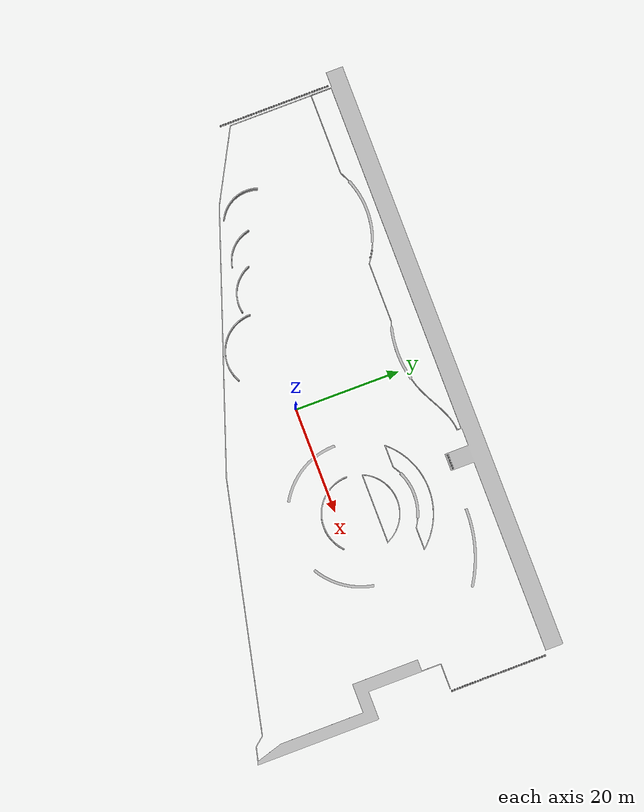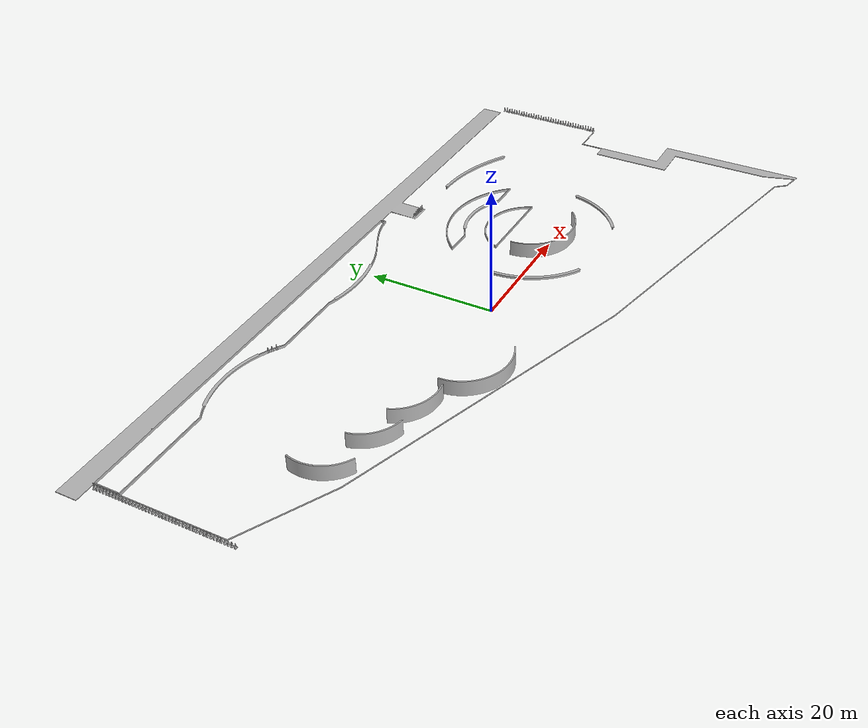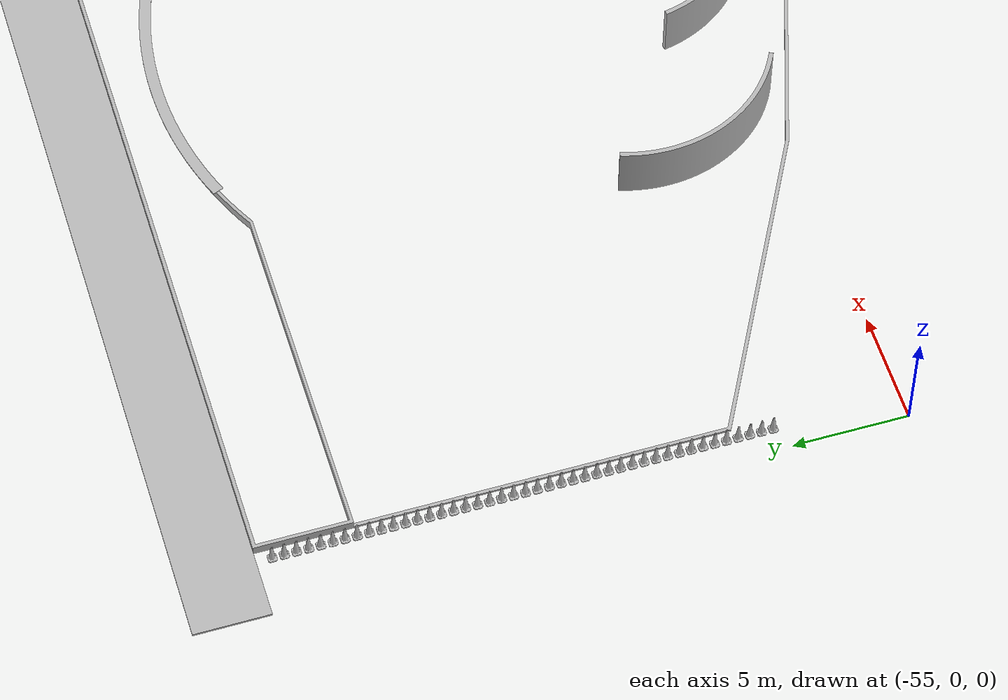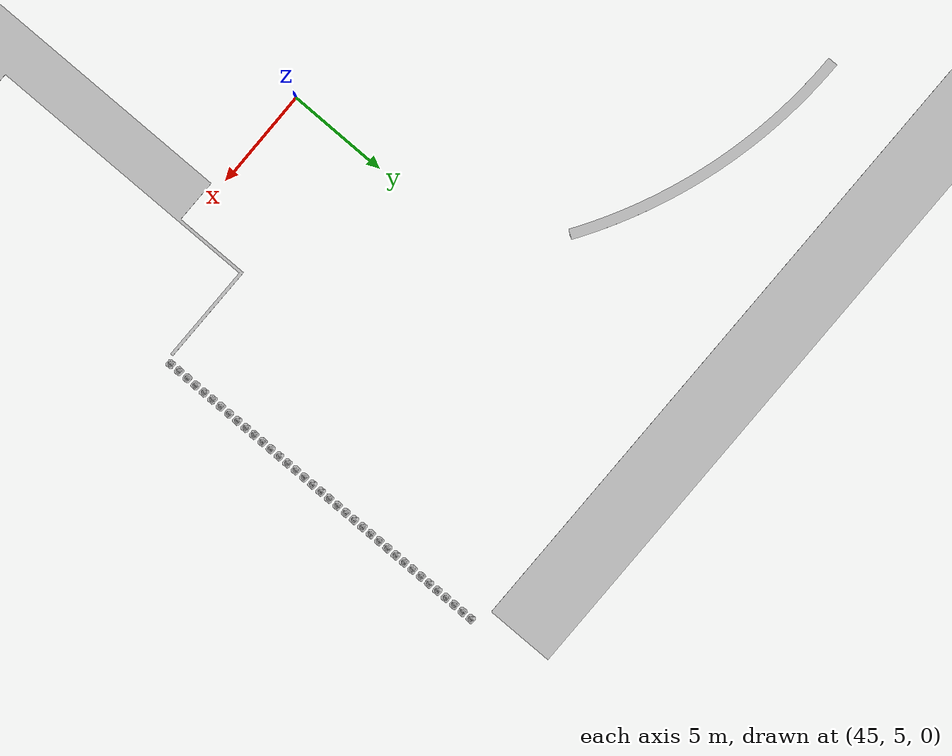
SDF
<?xml version="1.0"?>
<sdf version="1.4">
  <world name="default">
    <include>
      <uri>model://sun</uri>
    </include>
    <include>
      <uri>model://senai_cimatec</uri>
    </include>
    <model name='Construction Cone 00'>
      <link name='link'>
        <collision name='collision'>
          <geometry>
            <mesh>
              <scale>7.5 7.5 7.5</scale>
              <uri>model://construction_cone/meshes/construction_cone.dae</uri>
            </mesh>
          </geometry>
          <max_contacts>10</max_contacts>
          <surface>
            <bounce/>
            <friction>
              <ode/>
            </friction>
            <contact>
              <ode/>
            </contact>
          </surface>
        </collision>
        <visual name='visual'>
          <geometry>
            <mesh>
              <scale>7.5 7.5 7.5</scale>
              <uri>model://construction_cone/meshes/construction_cone.dae</uri>
            </mesh>
          </geometry>
        </visual>
        <velocity_decay>
          <linear>0</linear>
          <angular>0</angular>
        </velocity_decay>
        <self_collide>0</self_collide>
        <inertial>
          <inertia>
            <ixx>1</ixx>
            <ixy>0</ixy>
            <ixz>0</ixz>
            <iyy>1</iyy>
            <iyz>0</iyz>
            <izz>1</izz>
          </inertia>
          <mass>1</mass>
        </inertial>
        <kinematic>0</kinematic>
        <gravity>1</gravity>
      </link>
      <pose>58 8.5 0 0 -0 0</pose>
      <static>0</static>
    </model>
    <model name='Construction Cone 01'>
      <link name='link'>
        <collision name='collision'>
          <geometry>
            <mesh>
              <scale>7.5 7.5 7.5</scale>
              <uri>model://construction_cone/meshes/construction_cone.dae</uri>
            </mesh>
          </geometry>
          <max_contacts>10</max_contacts>
          <surface>
            <bounce/>
            <friction>
              <ode/>
            </friction>
            <contact>
              <ode/>
            </contact>
          </surface>
        </collision>
        <visual name='visual'>
          <geometry>
            <mesh>
              <scale>7.5 7.5 7.5</scale>
              <uri>model://construction_cone/meshes/construction_cone.dae</uri>
            </mesh>
          </geometry>
        </visual>
        <velocity_decay>
          <linear>0</linear>
          <angular>0</angular>
        </velocity_decay>
        <self_collide>0</self_collide>
        <inertial>
          <inertia>
            <ixx>1</ixx>
            <ixy>0</ixy>
            <ixz>0</ixz>
            <iyy>1</iyy>
            <iyz>0</iyz>
            <izz>1</izz>
          </inertia>
          <mass>1</mass>
        </inertial>
        <kinematic>0</kinematic>
        <gravity>1</gravity>
      </link>
      <pose>58 9 0 0 -0 0</pose>
      <static>0</static>
    </model>
    <model name='Construction Cone 02'>
      <link name='link'>
        <collision name='collision'>
          <geometry>
            <mesh>
              <scale>7.5 7.5 7.5</scale>
              <uri>model://construction_cone/meshes/construction_cone.dae</uri>
            </mesh>
          </geometry>
          <max_contacts>10</max_contacts>
          <surface>
            <bounce/>
            <friction>
              <ode/>
            </friction>
            <contact>
              <ode/>
            </contact>
          </surface>
        </collision>
        <visual name='visual'>
          <geometry>
            <mesh>
              <scale>7.5 7.5 7.5</scale>
              <uri>model://construction_cone/meshes/construction_cone.dae</uri>
            </mesh>
          </geometry>
        </visual>
        <velocity_decay>
          <linear>0</linear>
          <angular>0</angular>
        </velocity_decay>
        <self_collide>0</self_collide>
        <inertial>
          <inertia>
            <ixx>1</ixx>
            <ixy>0</ixy>
            <ixz>0</ixz>
            <iyy>1</iyy>
            <iyz>0</iyz>
            <izz>1</izz>
          </inertia>
          <mass>1</mass>
        </inertial>
        <kinematic>0</kinematic>
        <gravity>1</gravity>
      </link>
      <pose>58 9.5 0 0 -0 0</pose>
      <static>0</static>
    </model>
    <model name='Construction Cone 03'>
      <link name='link'>
        <collision name='collision'>
          <geometry>
            <mesh>
              <scale>7.5 7.5 7.5</scale>
              <uri>model://construction_cone/meshes/construction_cone.dae</uri>
            </mesh>
          </geometry>
          <max_contacts>10</max_contacts>
          <surface>
            <bounce/>
            <friction>
              <ode/>
            </friction>
            <contact>
              <ode/>
            </contact>
          </surface>
        </collision>
        <visual name='visual'>
          <geometry>
            <mesh>
              <scale>7.5 7.5 7.5</scale>
              <uri>model://construction_cone/meshes/construction_cone.dae</uri>
            </mesh>
          </geometry>
        </visual>
        <velocity_decay>
          <linear>0</linear>
          <angular>0</angular>
        </velocity_decay>
        <self_collide>0</self_collide>
        <inertial>
          <inertia>
            <ixx>1</ixx>
            <ixy>0</ixy>
            <ixz>0</ixz>
            <iyy>1</iyy>
            <iyz>0</iyz>
            <izz>1</izz>
          </inertia>
          <mass>1</mass>
        </inertial>
        <kinematic>0</kinematic>
        <gravity>1</gravity>
      </link>
      <pose>58 10 0 0 -0 0</pose>
      <static>0</static>
    </model>
    <model name='Construction Cone 04'>
      <link name='link'>
        <collision name='collision'>
          <geometry>
            <mesh>
              <scale>7.5 7.5 7.5</scale>
              <uri>model://construction_cone/meshes/construction_cone.dae</uri>
            </mesh>
          </geometry>
          <max_contacts>10</max_contacts>
          <surface>
            <bounce/>
            <friction>
              <ode/>
            </friction>
            <contact>
              <ode/>
            </contact>
          </surface>
        </collision>
        <visual name='visual'>
          <geometry>
            <mesh>
              <scale>7.5 7.5 7.5</scale>
              <uri>model://construction_cone/meshes/construction_cone.dae</uri>
            </mesh>
          </geometry>
        </visual>
        <velocity_decay>
          <linear>0</linear>
          <angular>0</angular>
        </velocity_decay>
        <self_collide>0</self_collide>
        <inertial>
          <inertia>
            <ixx>1</ixx>
            <ixy>0</ixy>
            <ixz>0</ixz>
            <iyy>1</iyy>
            <iyz>0</iyz>
            <izz>1</izz>
          </inertia>
          <mass>1</mass>
        </inertial>
        <kinematic>0</kinematic>
        <gravity>1</gravity>
      </link>
      <pose>58 10.5 0 0 -0 0</pose>
      <static>0</static>
    </model>
    <model name='Construction Cone 05'>
      <link name='link'>
        <collision name='collision'>
          <geometry>
            <mesh>
              <scale>7.5 7.5 7.5</scale>
              <uri>model://construction_cone/meshes/construction_cone.dae</uri>
            </mesh>
          </geometry>
          <max_contacts>10</max_contacts>
          <surface>
            <bounce/>
            <friction>
              <ode/>
            </friction>
            <contact>
              <ode/>
            </contact>
          </surface>
        </collision>
        <visual name='visual'>
          <geometry>
            <mesh>
              <scale>7.5 7.5 7.5</scale>
              <uri>model://construction_cone/meshes/construction_cone.dae</uri>
            </mesh>
          </geometry>
        </visual>
        <velocity_decay>
          <linear>0</linear>
          <angular>0</angular>
        </velocity_decay>
        <self_collide>0</self_collide>
        <inertial>
          <inertia>
            <ixx>1</ixx>
            <ixy>0</ixy>
            <ixz>0</ixz>
            <iyy>1</iyy>
            <iyz>0</iyz>
            <izz>1</izz>
          </inertia>
          <mass>1</mass>
        </inertial>
        <kinematic>0</kinematic>
        <gravity>1</gravity>
      </link>
      <pose>58 11 0 0 -0 0</pose>
      <static>0</static>
    </model>
    <model name='Construction Cone 06'>
      <link name='link'>
        <collision name='collision'>
          <geometry>
            <mesh>
              <scale>7.5 7.5 7.5</scale>
              <uri>model://construction_cone/meshes/construction_cone.dae</uri>
            </mesh>
          </geometry>
          <max_contacts>10</max_contacts>
          <surface>
            <bounce/>
            <friction>
              <ode/>
            </friction>
            <contact>
              <ode/>
            </contact>
          </surface>
        </collision>
        <visual name='visual'>
          <geometry>
            <mesh>
              <scale>7.5 7.5 7.5</scale>
              <uri>model://construction_cone/meshes/construction_cone.dae</uri>
            </mesh>
          </geometry>
        </visual>
        <velocity_decay>
          <linear>0</linear>
          <angular>0</angular>
        </velocity_decay>
        <self_collide>0</self_collide>
        <inertial>
          <inertia>
            <ixx>1</ixx>
            <ixy>0</ixy>
            <ixz>0</ixz>
            <iyy>1</iyy>
            <iyz>0</iyz>
            <izz>1</izz>
          </inertia>
          <mass>1</mass>
        </inertial>
        <kinematic>0</kinematic>
        <gravity>1</gravity>
      </link>
      <pose>58 11.5 0 0 -0 0</pose>
      <static>0</static>
    </model>
    <model name='Construction Cone 07'>
      <link name='link'>
        <collision name='collision'>
          <geometry>
            <mesh>
              <scale>7.5 7.5 7.5</scale>
              <uri>model://construction_cone/meshes/construction_cone.dae</uri>
            </mesh>
          </geometry>
          <max_contacts>10</max_contacts>
          <surface>
            <bounce/>
            <friction>
              <ode/>
            </friction>
            <contact>
              <ode/>
            </contact>
          </surface>
        </collision>
        <visual name='visual'>
          <geometry>
            <mesh>
              <scale>7.5 7.5 7.5</scale>
              <uri>model://construction_cone/meshes/construction_cone.dae</uri>
            </mesh>
          </geometry>
        </visual>
        <velocity_decay>
          <linear>0</linear>
          <angular>0</angular>
        </velocity_decay>
        <self_collide>0</self_collide>
        <inertial>
          <inertia>
            <ixx>1</ixx>
            <ixy>0</ixy>
            <ixz>0</ixz>
            <iyy>1</iyy>
            <iyz>0</iyz>
            <izz>1</izz>
          </inertia>
          <mass>1</mass>
        </inertial>
        <kinematic>0</kinematic>
        <gravity>1</gravity>
      </link>
      <pose>58 12 0 0 -0 0</pose>
      <static>0</static>
    </model>
    <model name='Construction Cone 08'>
      <link name='link'>
        <collision name='collision'>
          <geometry>
            <mesh>
              <scale>7.5 7.5 7.5</scale>
              <uri>model://construction_cone/meshes/construction_cone.dae</uri>
            </mesh>
          </geometry>
          <max_contacts>10</max_contacts>
          <surface>
            <bounce/>
            <friction>
              <ode/>
            </friction>
            <contact>
              <ode/>
            </contact>
          </surface>
        </collision>
        <visual name='visual'>
          <geometry>
            <mesh>
              <scale>7.5 7.5 7.5</scale>
              <uri>model://construction_cone/meshes/construction_cone.dae</uri>
            </mesh>
          </geometry>
        </visual>
        <velocity_decay>
          <linear>0</linear>
          <angular>0</angular>
        </velocity_decay>
        <self_collide>0</self_collide>
        <inertial>
          <inertia>
            <ixx>1</ixx>
            <ixy>0</ixy>
            <ixz>0</ixz>
            <iyy>1</iyy>
            <iyz>0</iyz>
            <izz>1</izz>
          </inertia>
          <mass>1</mass>
        </inertial>
        <kinematic>0</kinematic>
        <gravity>1</gravity>
      </link>
      <pose>58 12.5 0 0 -0 0</pose>
      <static>0</static>
    </model>
    <model name='Construction Cone 09'>
      <link name='link'>
        <collision name='collision'>
          <geometry>
            <mesh>
              <scale>7.5 7.5 7.5</scale>
              <uri>model://construction_cone/meshes/construction_cone.dae</uri>
            </mesh>
          </geometry>
          <max_contacts>10</max_contacts>
          <surface>
            <bounce/>
            <friction>
              <ode/>
            </friction>
            <contact>
              <ode/>
            </contact>
          </surface>
        </collision>
        <visual name='visual'>
          <geometry>
            <mesh>
              <scale>7.5 7.5 7.5</scale>
              <uri>model://construction_cone/meshes/construction_cone.dae</uri>
            </mesh>
          </geometry>
        </visual>
        <velocity_decay>
          <linear>0</linear>
          <angular>0</angular>
        </velocity_decay>
        <self_collide>0</self_collide>
        <inertial>
          <inertia>
            <ixx>1</ixx>
            <ixy>0</ixy>
            <ixz>0</ixz>
            <iyy>1</iyy>
            <iyz>0</iyz>
            <izz>1</izz>
          </inertia>
          <mass>1</mass>
        </inertial>
        <kinematic>0</kinematic>
        <gravity>1</gravity>
      </link>
      <pose>58 13 0 0 -0 0</pose>
      <static>0</static>
    </model>
    <model name='Construction Cone 10'>
      <link name='link'>
        <collision name='collision'>
          <geometry>
            <mesh>
              <scale>7.5 7.5 7.5</scale>
              <uri>model://construction_cone/meshes/construction_cone.dae</uri>
            </mesh>
          </geometry>
          <max_contacts>10</max_contacts>
          <surface>
            <bounce/>
            <friction>
              <ode/>
            </friction>
            <contact>
              <ode/>
            </contact>
          </surface>
        </collision>
        <visual name='visual'>
          <geometry>
            <mesh>
              <scale>7.5 7.5 7.5</scale>
              <uri>model://construction_cone/meshes/construction_cone.dae</uri>
            </mesh>
          </geometry>
        </visual>
        <velocity_decay>
          <linear>0</linear>
          <angular>0</angular>
        </velocity_decay>
        <self_collide>0</self_collide>
        <inertial>
          <inertia>
            <ixx>1</ixx>
            <ixy>0</ixy>
            <ixz>0</ixz>
            <iyy>1</iyy>
            <iyz>0</iyz>
            <izz>1</izz>
          </inertia>
          <mass>1</mass>
        </inertial>
        <kinematic>0</kinematic>
        <gravity>1</gravity>
      </link>
      <pose>58 13.5 0 0 -0 0</pose>
      <static>0</static>
    </model>
    <model name='Construction Cone 11'>
      <link name='link'>
        <collision name='collision'>
          <geometry>
            <mesh>
              <scale>7.5 7.5 7.5</scale>
              <uri>model://construction_cone/meshes/construction_cone.dae</uri>
            </mesh>
          </geometry>
          <max_contacts>10</max_contacts>
          <surface>
            <bounce/>
            <friction>
              <ode/>
            </friction>
            <contact>
              <ode/>
            </contact>
          </surface>
        </collision>
        <visual name='visual'>
          <geometry>
            <mesh>
              <scale>7.5 7.5 7.5</scale>
              <uri>model://construction_cone/meshes/construction_cone.dae</uri>
            </mesh>
          </geometry>
        </visual>
        <velocity_decay>
          <linear>0</linear>
          <angular>0</angular>
        </velocity_decay>
        <self_collide>0</self_collide>
        <inertial>
          <inertia>
            <ixx>1</ixx>
            <ixy>0</ixy>
            <ixz>0</ixz>
            <iyy>1</iyy>
            <iyz>0</iyz>
            <izz>1</izz>
          </inertia>
          <mass>1</mass>
        </inertial>
        <kinematic>0</kinematic>
        <gravity>1</gravity>
      </link>
      <pose>58 14 0 0 -0 0</pose>
      <static>0</static>
    </model>
    <model name='Construction Cone 12'>
      <link name='link'>
        <collision name='collision'>
          <geometry>
            <mesh>
              <scale>7.5 7.5 7.5</scale>
              <uri>model://construction_cone/meshes/construction_cone.dae</uri>
            </mesh>
          </geometry>
          <max_contacts>10</max_contacts>
          <surface>
            <bounce/>
            <friction>
              <ode/>
            </friction>
            <contact>
              <ode/>
            </contact>
          </surface>
        </collision>
        <visual name='visual'>
          <geometry>
            <mesh>
              <scale>7.5 7.5 7.5</scale>
              <uri>model://construction_cone/meshes/construction_cone.dae</uri>
            </mesh>
          </geometry>
        </visual>
        <velocity_decay>
          <linear>0</linear>
          <angular>0</angular>
        </velocity_decay>
        <self_collide>0</self_collide>
        <inertial>
          <inertia>
            <ixx>1</ixx>
            <ixy>0</ixy>
            <ixz>0</ixz>
            <iyy>1</iyy>
            <iyz>0</iyz>
            <izz>1</izz>
          </inertia>
          <mass>1</mass>
        </inertial>
        <kinematic>0</kinematic>
        <gravity>1</gravity>
      </link>
      <pose>58 14.5 0 0 -0 0</pose>
      <static>0</static>
    </model>
    <model name='Construction Cone 13'>
      <link name='link'>
        <collision name='collision'>
          <geometry>
            <mesh>
              <scale>7.5 7.5 7.5</scale>
              <uri>model://construction_cone/meshes/construction_cone.dae</uri>
            </mesh>
          </geometry>
          <max_contacts>10</max_contacts>
          <surface>
            <bounce/>
            <friction>
              <ode/>
            </friction>
            <contact>
              <ode/>
            </contact>
          </surface>
        </collision>
        <visual name='visual'>
          <geometry>
            <mesh>
              <scale>7.5 7.5 7.5</scale>
              <uri>model://construction_cone/meshes/construction_cone.dae</uri>
            </mesh>
          </geometry>
        </visual>
        <velocity_decay>
          <linear>0</linear>
          <angular>0</angular>
        </velocity_decay>
        <self_collide>0</self_collide>
        <inertial>
          <inertia>
            <ixx>1</ixx>
            <ixy>0</ixy>
            <ixz>0</ixz>
            <iyy>1</iyy>
            <iyz>0</iyz>
            <izz>1</izz>
          </inertia>
          <mass>1</mass>
        </inertial>
        <kinematic>0</kinematic>
        <gravity>1</gravity>
      </link>
      <pose>58 15 0 0 -0 0</pose>
      <static>0</static>
    </model>
    <model name='Construction Cone 14'>
      <link name='link'>
        <collision name='collision'>
          <geometry>
            <mesh>
              <scale>7.5 7.5 7.5</scale>
              <uri>model://construction_cone/meshes/construction_cone.dae</uri>
            </mesh>
          </geometry>
          <max_contacts>10</max_contacts>
          <surface>
            <bounce/>
            <friction>
              <ode/>
            </friction>
            <contact>
              <ode/>
            </contact>
          </surface>
        </collision>
        <visual name='visual'>
          <geometry>
            <mesh>
              <scale>7.5 7.5 7.5</scale>
              <uri>model://construction_cone/meshes/construction_cone.dae</uri>
            </mesh>
          </geometry>
        </visual>
        <velocity_decay>
          <linear>0</linear>
          <angular>0</angular>
        </velocity_decay>
        <self_collide>0</self_collide>
        <inertial>
          <inertia>
            <ixx>1</ixx>
            <ixy>0</ixy>
            <ixz>0</ixz>
            <iyy>1</iyy>
            <iyz>0</iyz>
            <izz>1</izz>
          </inertia>
          <mass>1</mass>
        </inertial>
        <kinematic>0</kinematic>
        <gravity>1</gravity>
      </link>
      <pose>58 15.5 0 0 -0 0</pose>
      <static>0</static>
    </model>
    <model name='Construction Cone 15'>
      <link name='link'>
        <collision name='collision'>
          <geometry>
            <mesh>
              <scale>7.5 7.5 7.5</scale>
              <uri>model://construction_cone/meshes/construction_cone.dae</uri>
            </mesh>
          </geometry>
          <max_contacts>10</max_contacts>
          <surface>
            <bounce/>
            <friction>
              <ode/>
            </friction>
            <contact>
              <ode/>
            </contact>
          </surface>
        </collision>
        <visual name='visual'>
          <geometry>
            <mesh>
              <scale>7.5 7.5 7.5</scale>
              <uri>model://construction_cone/meshes/construction_cone.dae</uri>
            </mesh>
          </geometry>
        </visual>
        <velocity_decay>
          <linear>0</linear>
          <angular>0</angular>
        </velocity_decay>
        <self_collide>0</self_collide>
        <inertial>
          <inertia>
            <ixx>1</ixx>
            <ixy>0</ixy>
            <ixz>0</ixz>
            <iyy>1</iyy>
            <iyz>0</iyz>
            <izz>1</izz>
          </inertia>
          <mass>1</mass>
        </inertial>
        <kinematic>0</kinematic>
        <gravity>1</gravity>
      </link>
      <pose>58 16 0 0 -0 0</pose>
      <static>0</static>
    </model>
    <model name='Construction Cone 16'>
      <link name='link'>
        <collision name='collision'>
          <geometry>
            <mesh>
              <scale>7.5 7.5 7.5</scale>
              <uri>model://construction_cone/meshes/construction_cone.dae</uri>
            </mesh>
          </geometry>
          <max_contacts>10</max_contacts>
          <surface>
            <bounce/>
            <friction>
              <ode/>
            </friction>
            <contact>
              <ode/>
            </contact>
          </surface>
        </collision>
        <visual name='visual'>
          <geometry>
            <mesh>
              <scale>7.5 7.5 7.5</scale>
              <uri>model://construction_cone/meshes/construction_cone.dae</uri>
            </mesh>
          </geometry>
        </visual>
        <velocity_decay>
          <linear>0</linear>
          <angular>0</angular>
        </velocity_decay>
        <self_collide>0</self_collide>
        <inertial>
          <inertia>
            <ixx>1</ixx>
            <ixy>0</ixy>
            <ixz>0</ixz>
            <iyy>1</iyy>
            <iyz>0</iyz>
            <izz>1</izz>
          </inertia>
          <mass>1</mass>
        </inertial>
        <kinematic>0</kinematic>
        <gravity>1</gravity>
      </link>
      <pose>58 16.5 0 0 -0 0</pose>
      <static>0</static>
    </model>
    <model name='Construction Cone 17'>
      <link name='link'>
        <collision name='collision'>
          <geometry>
            <mesh>
              <scale>7.5 7.5 7.5</scale>
              <uri>model://construction_cone/meshes/construction_cone.dae</uri>
            </mesh>
          </geometry>
          <max_contacts>10</max_contacts>
          <surface>
            <bounce/>
            <friction>
              <ode/>
            </friction>
            <contact>
              <ode/>
            </contact>
          </surface>
        </collision>
        <visual name='visual'>
          <geometry>
            <mesh>
              <scale>7.5 7.5 7.5</scale>
              <uri>model://construction_cone/meshes/construction_cone.dae</uri>
            </mesh>
          </geometry>
        </visual>
        <velocity_decay>
          <linear>0</linear>
          <angular>0</angular>
        </velocity_decay>
        <self_collide>0</self_collide>
        <inertial>
          <inertia>
            <ixx>1</ixx>
            <ixy>0</ixy>
            <ixz>0</ixz>
            <iyy>1</iyy>
            <iyz>0</iyz>
            <izz>1</izz>
          </inertia>
          <mass>1</mass>
        </inertial>
        <kinematic>0</kinematic>
        <gravity>1</gravity>
      </link>
      <pose>58 17 0 0 -0 0</pose>
      <static>0</static>
    </model>
    <model name='Construction Cone 18'>
      <link name='link'>
        <collision name='collision'>
          <geometry>
            <mesh>
              <scale>7.5 7.5 7.5</scale>
              <uri>model://construction_cone/meshes/construction_cone.dae</uri>
            </mesh>
          </geometry>
          <max_contacts>10</max_contacts>
          <surface>
            <bounce/>
            <friction>
              <ode/>
            </friction>
            <contact>
              <ode/>
            </contact>
          </surface>
        </collision>
        <visual name='visual'>
          <geometry>
            <mesh>
              <scale>7.5 7.5 7.5</scale>
              <uri>model://construction_cone/meshes/construction_cone.dae</uri>
            </mesh>
          </geometry>
        </visual>
        <velocity_decay>
          <linear>0</linear>
          <angular>0</angular>
        </velocity_decay>
        <self_collide>0</self_collide>
        <inertial>
          <inertia>
            <ixx>1</ixx>
            <ixy>0</ixy>
            <ixz>0</ixz>
            <iyy>1</iyy>
            <iyz>0</iyz>
            <izz>1</izz>
          </inertia>
          <mass>1</mass>
        </inertial>
        <kinematic>0</kinematic>
        <gravity>1</gravity>
      </link>
      <pose>58 17.5 0 0 -0 0</pose>
      <static>0</static>
    </model>
    <model name='Construction Cone 19'>
      <link name='link'>
        <collision name='collision'>
          <geometry>
            <mesh>
              <scale>7.5 7.5 7.5</scale>
              <uri>model://construction_cone/meshes/construction_cone.dae</uri>
            </mesh>
          </geometry>
          <max_contacts>10</max_contacts>
          <surface>
            <bounce/>
            <friction>
              <ode/>
            </friction>
            <contact>
              <ode/>
            </contact>
          </surface>
        </collision>
        <visual name='visual'>
          <geometry>
            <mesh>
              <scale>7.5 7.5 7.5</scale>
              <uri>model://construction_cone/meshes/construction_cone.dae</uri>
            </mesh>
          </geometry>
        </visual>
        <velocity_decay>
          <linear>0</linear>
          <angular>0</angular>
        </velocity_decay>
        <self_collide>0</self_collide>
        <inertial>
          <inertia>
            <ixx>1</ixx>
            <ixy>0</ixy>
            <ixz>0</ixz>
            <iyy>1</iyy>
            <iyz>0</iyz>
            <izz>1</izz>
          </inertia>
          <mass>1</mass>
        </inertial>
        <kinematic>0</kinematic>
        <gravity>1</gravity>
      </link>
      <pose>58 18 0 0 -0 0</pose>
      <static>0</static>
    </model>
    <model name='Construction Cone 20'>
      <link name='link'>
        <collision name='collision'>
          <geometry>
            <mesh>
              <scale>7.5 7.5 7.5</scale>
              <uri>model://construction_cone/meshes/construction_cone.dae</uri>
            </mesh>
          </geometry>
          <max_contacts>10</max_contacts>
          <surface>
            <bounce/>
            <friction>
              <ode/>
            </friction>
            <contact>
              <ode/>
            </contact>
          </surface>
        </collision>
        <visual name='visual'>
          <geometry>
            <mesh>
              <scale>7.5 7.5 7.5</scale>
              <uri>model://construction_cone/meshes/construction_cone.dae</uri>
            </mesh>
          </geometry>
        </visual>
        <velocity_decay>
          <linear>0</linear>
          <angular>0</angular>
        </velocity_decay>
        <self_collide>0</self_collide>
        <inertial>
          <inertia>
            <ixx>1</ixx>
            <ixy>0</ixy>
            <ixz>0</ixz>
            <iyy>1</iyy>
            <iyz>0</iyz>
            <izz>1</izz>
          </inertia>
          <mass>1</mass>
        </inertial>
        <kinematic>0</kinematic>
        <gravity>1</gravity>
      </link>
      <pose>58 18.5 0 0 -0 0</pose>
      <static>0</static>
    </model>
    <model name='Construction Cone 21'>
      <link name='link'>
        <collision name='collision'>
          <geometry>
            <mesh>
              <scale>7.5 7.5 7.5</scale>
              <uri>model://construction_cone/meshes/construction_cone.dae</uri>
            </mesh>
          </geometry>
          <max_contacts>10</max_contacts>
          <surface>
            <bounce/>
            <friction>
              <ode/>
            </friction>
            <contact>
              <ode/>
            </contact>
          </surface>
        </collision>
        <visual name='visual'>
          <geometry>
            <mesh>
              <scale>7.5 7.5 7.5</scale>
              <uri>model://construction_cone/meshes/construction_cone.dae</uri>
            </mesh>
          </geometry>
        </visual>
        <velocity_decay>
          <linear>0</linear>
          <angular>0</angular>
        </velocity_decay>
        <self_collide>0</self_collide>
        <inertial>
          <inertia>
            <ixx>1</ixx>
            <ixy>0</ixy>
            <ixz>0</ixz>
            <iyy>1</iyy>
            <iyz>0</iyz>
            <izz>1</izz>
          </inertia>
          <mass>1</mass>
        </inertial>
        <kinematic>0</kinematic>
        <gravity>1</gravity>
      </link>
      <pose>58 19 0 0 -0 0</pose>
      <static>0</static>
    </model>
    <model name='Construction Cone 22'>
      <link name='link'>
        <collision name='collision'>
          <geometry>
            <mesh>
              <scale>7.5 7.5 7.5</scale>
              <uri>model://construction_cone/meshes/construction_cone.dae</uri>
            </mesh>
          </geometry>
          <max_contacts>10</max_contacts>
          <surface>
            <bounce/>
            <friction>
              <ode/>
            </friction>
            <contact>
              <ode/>
            </contact>
          </surface>
        </collision>
        <visual name='visual'>
          <geometry>
            <mesh>
              <scale>7.5 7.5 7.5</scale>
              <uri>model://construction_cone/meshes/construction_cone.dae</uri>
            </mesh>
          </geometry>
        </visual>
        <velocity_decay>
          <linear>0</linear>
          <angular>0</angular>
        </velocity_decay>
        <self_collide>0</self_collide>
        <inertial>
          <inertia>
            <ixx>1</ixx>
            <ixy>0</ixy>
            <ixz>0</ixz>
            <iyy>1</iyy>
            <iyz>0</iyz>
            <izz>1</izz>
          </inertia>
          <mass>1</mass>
        </inertial>
        <kinematic>0</kinematic>
        <gravity>1</gravity>
      </link>
      <pose>58 19.5 0 0 -0 0</pose>
      <static>0</static>
    </model>
    <model name='Construction Cone 23'>
      <link name='link'>
        <collision name='collision'>
          <geometry>
            <mesh>
              <scale>7.5 7.5 7.5</scale>
              <uri>model://construction_cone/meshes/construction_cone.dae</uri>
            </mesh>
          </geometry>
          <max_contacts>10</max_contacts>
          <surface>
            <bounce/>
            <friction>
              <ode/>
            </friction>
            <contact>
              <ode/>
            </contact>
          </surface>
        </collision>
        <visual name='visual'>
          <geometry>
            <mesh>
              <scale>7.5 7.5 7.5</scale>
              <uri>model://construction_cone/meshes/construction_cone.dae</uri>
            </mesh>
          </geometry>
        </visual>
        <velocity_decay>
          <linear>0</linear>
          <angular>0</angular>
        </velocity_decay>
        <self_collide>0</self_collide>
        <inertial>
          <inertia>
            <ixx>1</ixx>
            <ixy>0</ixy>
            <ixz>0</ixz>
            <iyy>1</iyy>
            <iyz>0</iyz>
            <izz>1</izz>
          </inertia>
          <mass>1</mass>
        </inertial>
        <kinematic>0</kinematic>
        <gravity>1</gravity>
      </link>
      <pose>58 20 0 0 -0 0</pose>
      <static>0</static>
    </model>
    <model name='Construction Cone 24'>
      <link name='link'>
        <collision name='collision'>
          <geometry>
            <mesh>
              <scale>7.5 7.5 7.5</scale>
              <uri>model://construction_cone/meshes/construction_cone.dae</uri>
            </mesh>
          </geometry>
          <max_contacts>10</max_contacts>
          <surface>
            <bounce/>
            <friction>
              <ode/>
            </friction>
            <contact>
              <ode/>
            </contact>
          </surface>
        </collision>
        <visual name='visual'>
          <geometry>
            <mesh>
              <scale>7.5 7.5 7.5</scale>
              <uri>model://construction_cone/meshes/construction_cone.dae</uri>
            </mesh>
          </geometry>
        </visual>
        <velocity_decay>
          <linear>0</linear>
          <angular>0</angular>
        </velocity_decay>
        <self_collide>0</self_collide>
        <inertial>
          <inertia>
            <ixx>1</ixx>
            <ixy>0</ixy>
            <ixz>0</ixz>
            <iyy>1</iyy>
            <iyz>0</iyz>
            <izz>1</izz>
          </inertia>
          <mass>1</mass>
        </inertial>
        <kinematic>0</kinematic>
        <gravity>1</gravity>
      </link>
      <pose>58 20.5 0 0 -0 0</pose>
      <static>0</static>
    </model>
    <model name='Construction Cone 25'>
      <link name='link'>
        <collision name='collision'>
          <geometry>
            <mesh>
              <scale>7.5 7.5 7.5</scale>
              <uri>model://construction_cone/meshes/construction_cone.dae</uri>
            </mesh>
          </geometry>
          <max_contacts>10</max_contacts>
          <surface>
            <bounce/>
            <friction>
              <ode/>
            </friction>
            <contact>
              <ode/>
            </contact>
          </surface>
        </collision>
        <visual name='visual'>
          <geometry>
            <mesh>
              <scale>7.5 7.5 7.5</scale>
              <uri>model://construction_cone/meshes/construction_cone.dae</uri>
            </mesh>
          </geometry>
        </visual>
        <velocity_decay>
          <linear>0</linear>
          <angular>0</angular>
        </velocity_decay>
        <self_collide>0</self_collide>
        <inertial>
          <inertia>
            <ixx>1</ixx>
            <ixy>0</ixy>
            <ixz>0</ixz>
            <iyy>1</iyy>
            <iyz>0</iyz>
            <izz>1</izz>
          </inertia>
          <mass>1</mass>
        </inertial>
        <kinematic>0</kinematic>
        <gravity>1</gravity>
      </link>
      <pose>58 21 0 0 -0 0</pose>
      <static>0</static>
    </model>
    <model name='Construction Cone 26'>
      <link name='link'>
        <collision name='collision'>
          <geometry>
            <mesh>
              <scale>7.5 7.5 7.5</scale>
              <uri>model://construction_cone/meshes/construction_cone.dae</uri>
            </mesh>
          </geometry>
          <max_contacts>10</max_contacts>
          <surface>
            <bounce/>
            <friction>
              <ode/>
            </friction>
            <contact>
              <ode/>
            </contact>
          </surface>
        </collision>
        <visual name='visual'>
          <geometry>
            <mesh>
              <scale>7.5 7.5 7.5</scale>
              <uri>model://construction_cone/meshes/construction_cone.dae</uri>
            </mesh>
          </geometry>
        </visual>
        <velocity_decay>
          <linear>0</linear>
          <angular>0</angular>
        </velocity_decay>
        <self_collide>0</self_collide>
        <inertial>
          <inertia>
            <ixx>1</ixx>
            <ixy>0</ixy>
            <ixz>0</ixz>
            <iyy>1</iyy>
            <iyz>0</iyz>
            <izz>1</izz>
          </inertia>
          <mass>1</mass>
        </inertial>
        <kinematic>0</kinematic>
        <gravity>1</gravity>
      </link>
      <pose>58 21.5 0 0 -0 0</pose>
      <static>0</static>
    </model>
    <model name='Construction Cone 27'>
      <link name='link'>
        <collision name='collision'>
          <geometry>
            <mesh>
              <scale>7.5 7.5 7.5</scale>
              <uri>model://construction_cone/meshes/construction_cone.dae</uri>
            </mesh>
          </geometry>
          <max_contacts>10</max_contacts>
          <surface>
            <bounce/>
            <friction>
              <ode/>
            </friction>
            <contact>
              <ode/>
            </contact>
          </surface>
        </collision>
        <visual name='visual'>
          <geometry>
            <mesh>
              <scale>7.5 7.5 7.5</scale>
              <uri>model://construction_cone/meshes/construction_cone.dae</uri>
            </mesh>
          </geometry>
        </visual>
        <velocity_decay>
          <linear>0</linear>
          <angular>0</angular>
        </velocity_decay>
        <self_collide>0</self_collide>
        <inertial>
          <inertia>
            <ixx>1</ixx>
            <ixy>0</ixy>
            <ixz>0</ixz>
            <iyy>1</iyy>
            <iyz>0</iyz>
            <izz>1</izz>
          </inertia>
          <mass>1</mass>
        </inertial>
        <kinematic>0</kinematic>
        <gravity>1</gravity>
      </link>
      <pose>58 22 0 0 -0 0</pose>
      <static>0</static>
    </model>
    <model name='Construction Cone 28'>
      <link name='link'>
        <collision name='collision'>
          <geometry>
            <mesh>
              <scale>7.5 7.5 7.5</scale>
              <uri>model://construction_cone/meshes/construction_cone.dae</uri>
            </mesh>
          </geometry>
          <max_contacts>10</max_contacts>
          <surface>
            <bounce/>
            <friction>
              <ode/>
            </friction>
            <contact>
              <ode/>
            </contact>
          </surface>
        </collision>
        <visual name='visual'>
          <geometry>
            <mesh>
              <scale>7.5 7.5 7.5</scale>
              <uri>model://construction_cone/meshes/construction_cone.dae</uri>
            </mesh>
          </geometry>
        </visual>
        <velocity_decay>
          <linear>0</linear>
          <angular>0</angular>
        </velocity_decay>
        <self_collide>0</self_collide>
        <inertial>
          <inertia>
            <ixx>1</ixx>
            <ixy>0</ixy>
            <ixz>0</ixz>
            <iyy>1</iyy>
            <iyz>0</iyz>
            <izz>1</izz>
          </inertia>
          <mass>1</mass>
        </inertial>
        <kinematic>0</kinematic>
        <gravity>1</gravity>
      </link>
      <pose>58 22.5 0 0 -0 0</pose>
      <static>0</static>
    </model>
    <model name='Construction Cone 29'>
      <link name='link'>
        <collision name='collision'>
          <geometry>
            <mesh>
              <scale>7.5 7.5 7.5</scale>
              <uri>model://construction_cone/meshes/construction_cone.dae</uri>
            </mesh>
          </geometry>
          <max_contacts>10</max_contacts>
          <surface>
            <bounce/>
            <friction>
              <ode/>
            </friction>
            <contact>
              <ode/>
            </contact>
          </surface>
        </collision>
        <visual name='visual'>
          <geometry>
            <mesh>
              <scale>7.5 7.5 7.5</scale>
              <uri>model://construction_cone/meshes/construction_cone.dae</uri>
            </mesh>
          </geometry>
        </visual>
        <velocity_decay>
          <linear>0</linear>
          <angular>0</angular>
        </velocity_decay>
        <self_collide>0</self_collide>
        <inertial>
          <inertia>
            <ixx>1</ixx>
            <ixy>0</ixy>
            <ixz>0</ixz>
            <iyy>1</iyy>
            <iyz>0</iyz>
            <izz>1</izz>
          </inertia>
          <mass>1</mass>
        </inertial>
        <kinematic>0</kinematic>
        <gravity>1</gravity>
      </link>
      <pose>58 23 0 0 -0 0</pose>
      <static>0</static>
    </model>
    <model name='Construction Cone 30'>
      <link name='link'>
        <collision name='collision'>
          <geometry>
            <mesh>
              <scale>7.5 7.5 7.5</scale>
              <uri>model://construction_cone/meshes/construction_cone.dae</uri>
            </mesh>
          </geometry>
          <max_contacts>10</max_contacts>
          <surface>
            <bounce/>
            <friction>
              <ode/>
            </friction>
            <contact>
              <ode/>
            </contact>
          </surface>
        </collision>
        <visual name='visual'>
          <geometry>
            <mesh>
              <scale>7.5 7.5 7.5</scale>
              <uri>model://construction_cone/meshes/construction_cone.dae</uri>
            </mesh>
          </geometry>
        </visual>
        <velocity_decay>
          <linear>0</linear>
          <angular>0</angular>
        </velocity_decay>
        <self_collide>0</self_collide>
        <inertial>
          <inertia>
            <ixx>1</ixx>
            <ixy>0</ixy>
            <ixz>0</ixz>
            <iyy>1</iyy>
            <iyz>0</iyz>
            <izz>1</izz>
          </inertia>
          <mass>1</mass>
        </inertial>
        <kinematic>0</kinematic>
        <gravity>1</gravity>
      </link>
      <pose>58 23.5 0 0 -0 0</pose>
      <static>0</static>
    </model>
    <model name='Construction Cone 31'>
      <link name='link'>
        <collision name='collision'>
          <geometry>
            <mesh>
              <scale>7.5 7.5 7.5</scale>
              <uri>model://construction_cone/meshes/construction_cone.dae</uri>
            </mesh>
          </geometry>
          <max_contacts>10</max_contacts>
          <surface>
            <bounce/>
            <friction>
              <ode/>
            </friction>
            <contact>
              <ode/>
            </contact>
          </surface>
        </collision>
        <visual name='visual'>
          <geometry>
            <mesh>
              <scale>7.5 7.5 7.5</scale>
              <uri>model://construction_cone/meshes/construction_cone.dae</uri>
            </mesh>
          </geometry>
        </visual>
        <velocity_decay>
          <linear>0</linear>
          <angular>0</angular>
        </velocity_decay>
        <self_collide>0</self_collide>
        <inertial>
          <inertia>
            <ixx>1</ixx>
            <ixy>0</ixy>
            <ixz>0</ixz>
            <iyy>1</iyy>
            <iyz>0</iyz>
            <izz>1</izz>
          </inertia>
          <mass>1</mass>
        </inertial>
        <kinematic>0</kinematic>
        <gravity>1</gravity>
      </link>
      <pose>58 24 0 0 -0 0</pose>
      <static>0</static>
    </model>
    <model name='Construction Cone 32'>
      <link name='link'>
        <collision name='collision'>
          <geometry>
            <mesh>
              <scale>7.5 7.5 7.5</scale>
              <uri>model://construction_cone/meshes/construction_cone.dae</uri>
            </mesh>
          </geometry>
          <max_contacts>10</max_contacts>
          <surface>
            <bounce/>
            <friction>
              <ode/>
            </friction>
            <contact>
              <ode/>
            </contact>
          </surface>
        </collision>
        <visual name='visual'>
          <geometry>
            <mesh>
              <scale>7.5 7.5 7.5</scale>
              <uri>model://construction_cone/meshes/construction_cone.dae</uri>
            </mesh>
          </geometry>
        </visual>
        <velocity_decay>
          <linear>0</linear>
          <angular>0</angular>
        </velocity_decay>
        <self_collide>0</self_collide>
        <inertial>
          <inertia>
            <ixx>1</ixx>
            <ixy>0</ixy>
            <ixz>0</ixz>
            <iyy>1</iyy>
            <iyz>0</iyz>
            <izz>1</izz>
          </inertia>
          <mass>1</mass>
        </inertial>
        <kinematic>0</kinematic>
        <gravity>1</gravity>
      </link>
      <pose>58 24.5 0 0 -0 0</pose>
      <static>0</static>
    </model>
    <model name='Construction Cone 33'>
      <link name='link'>
        <collision name='collision'>
          <geometry>
            <mesh>
              <scale>7.5 7.5 7.5</scale>
              <uri>model://construction_cone/meshes/construction_cone.dae</uri>
            </mesh>
          </geometry>
          <max_contacts>10</max_contacts>
          <surface>
            <bounce/>
            <friction>
              <ode/>
            </friction>
            <contact>
              <ode/>
            </contact>
          </surface>
        </collision>
        <visual name='visual'>
          <geometry>
            <mesh>
              <scale>7.5 7.5 7.5</scale>
              <uri>model://construction_cone/meshes/construction_cone.dae</uri>
            </mesh>
          </geometry>
        </visual>
        <velocity_decay>
          <linear>0</linear>
          <angular>0</angular>
        </velocity_decay>
        <self_collide>0</self_collide>
        <inertial>
          <inertia>
            <ixx>1</ixx>
            <ixy>0</ixy>
            <ixz>0</ixz>
            <iyy>1</iyy>
            <iyz>0</iyz>
            <izz>1</izz>
          </inertia>
          <mass>1</mass>
        </inertial>
        <kinematic>0</kinematic>
        <gravity>1</gravity>
      </link>
      <pose>58 25 0 0 -0 0</pose>
      <static>0</static>
    </model>
    <model name='Construction Cone 34'>
      <link name='link'>
        <collision name='collision'>
          <geometry>
            <mesh>
              <scale>7.5 7.5 7.5</scale>
              <uri>model://construction_cone/meshes/construction_cone.dae</uri>
            </mesh>
          </geometry>
          <max_contacts>10</max_contacts>
          <surface>
            <bounce/>
            <friction>
              <ode/>
            </friction>
            <contact>
              <ode/>
            </contact>
          </surface>
        </collision>
        <visual name='visual'>
          <geometry>
            <mesh>
              <scale>7.5 7.5 7.5</scale>
              <uri>model://construction_cone/meshes/construction_cone.dae</uri>
            </mesh>
          </geometry>
        </visual>
        <velocity_decay>
          <linear>0</linear>
          <angular>0</angular>
        </velocity_decay>
        <self_collide>0</self_collide>
        <inertial>
          <inertia>
            <ixx>1</ixx>
            <ixy>0</ixy>
            <ixz>0</ixz>
            <iyy>1</iyy>
            <iyz>0</iyz>
            <izz>1</izz>
          </inertia>
          <mass>1</mass>
        </inertial>
        <kinematic>0</kinematic>
        <gravity>1</gravity>
      </link>
      <pose>58 25.5 0 0 -0 0</pose>
      <static>0</static>
    </model>
    <model name='Construction Cone 35'>
      <link name='link'>
        <collision name='collision'>
          <geometry>
            <mesh>
              <scale>7.5 7.5 7.5</scale>
              <uri>model://construction_cone/meshes/construction_cone.dae</uri>
            </mesh>
          </geometry>
          <max_contacts>10</max_contacts>
          <surface>
            <bounce/>
            <friction>
              <ode/>
            </friction>
            <contact>
              <ode/>
            </contact>
          </surface>
        </collision>
        <visual name='visual'>
          <geometry>
            <mesh>
              <scale>7.5 7.5 7.5</scale>
              <uri>model://construction_cone/meshes/construction_cone.dae</uri>
            </mesh>
          </geometry>
        </visual>
        <velocity_decay>
          <linear>0</linear>
          <angular>0</angular>
        </velocity_decay>
        <self_collide>0</self_collide>
        <inertial>
          <inertia>
            <ixx>1</ixx>
            <ixy>0</ixy>
            <ixz>0</ixz>
            <iyy>1</iyy>
            <iyz>0</iyz>
            <izz>1</izz>
          </inertia>
          <mass>1</mass>
        </inertial>
        <kinematic>0</kinematic>
        <gravity>1</gravity>
      </link>
      <pose>58 26 0 0 -0 0</pose>
      <static>0</static>
    </model>
    <model name='Construction Cone 36'>
      <link name='link'>
        <collision name='collision'>
          <geometry>
            <mesh>
              <scale>7.5 7.5 7.5</scale>
              <uri>model://construction_cone/meshes/construction_cone.dae</uri>
            </mesh>
          </geometry>
          <max_contacts>10</max_contacts>
          <surface>
            <bounce/>
            <friction>
              <ode/>
            </friction>
            <contact>
              <ode/>
            </contact>
          </surface>
        </collision>
        <visual name='visual'>
          <geometry>
            <mesh>
              <scale>7.5 7.5 7.5</scale>
              <uri>model://construction_cone/meshes/construction_cone.dae</uri>
            </mesh>
          </geometry>
        </visual>
        <velocity_decay>
          <linear>0</linear>
          <angular>0</angular>
        </velocity_decay>
        <self_collide>0</self_collide>
        <inertial>
          <inertia>
            <ixx>1</ixx>
            <ixy>0</ixy>
            <ixz>0</ixz>
            <iyy>1</iyy>
            <iyz>0</iyz>
            <izz>1</izz>
          </inertia>
          <mass>1</mass>
        </inertial>
        <kinematic>0</kinematic>
        <gravity>1</gravity>
      </link>
      <pose>58 26.5 0 0 -0 0</pose>
      <static>0</static>
    </model>

    <model name='Construction Cone Parking Lot 00'>
      <link name='link'>
        <collision name='collision'>
          <geometry>
            <mesh>
              <scale>7.5 7.5 7.5</scale>
              <uri>model://construction_cone/meshes/construction_cone.dae</uri>
            </mesh>
          </geometry>
          <max_contacts>10</max_contacts>
          <surface>
            <bounce/>
            <friction>
              <ode/>
            </friction>
            <contact>
              <ode/>
            </contact>
          </surface>
        </collision>
        <visual name='visual'>
          <geometry>
            <mesh>
              <scale>7.5 7.5 7.5</scale>
              <uri>model://construction_cone/meshes/construction_cone.dae</uri>
            </mesh>
          </geometry>
        </visual>
        <velocity_decay>
          <linear>0</linear>
          <angular>0</angular>
        </velocity_decay>
        <self_collide>0</self_collide>
        <inertial>
          <inertia>
            <ixx>1</ixx>
            <ixy>0</ixy>
            <ixz>0</ixz>
            <iyy>1</iyy>
            <iyz>0</iyz>
            <izz>1</izz>
          </inertia>
          <mass>1</mass>
        </inertial>
        <kinematic>0</kinematic>
        <gravity>1</gravity>
      </link>
      <pose>-54 5.5 0 0 -0 0</pose>
      <static>0</static>
    </model>
    <model name='Construction Cone Parking Lot 01'>
      <link name='link'>
        <collision name='collision'>
          <geometry>
            <mesh>
              <scale>7.5 7.5 7.5</scale>
              <uri>model://construction_cone/meshes/construction_cone.dae</uri>
            </mesh>
          </geometry>
          <max_contacts>10</max_contacts>
          <surface>
            <bounce/>
            <friction>
              <ode/>
            </friction>
            <contact>
              <ode/>
            </contact>
          </surface>
        </collision>
        <visual name='visual'>
          <geometry>
            <mesh>
              <scale>7.5 7.5 7.5</scale>
              <uri>model://construction_cone/meshes/construction_cone.dae</uri>
            </mesh>
          </geometry>
        </visual>
        <velocity_decay>
          <linear>0</linear>
          <angular>0</angular>
        </velocity_decay>
        <self_collide>0</self_collide>
        <inertial>
          <inertia>
            <ixx>1</ixx>
            <ixy>0</ixy>
            <ixz>0</ixz>
            <iyy>1</iyy>
            <iyz>0</iyz>
            <izz>1</izz>
          </inertia>
          <mass>1</mass>
        </inertial>
        <kinematic>0</kinematic>
        <gravity>1</gravity>
      </link>
      <pose>-54 6 0 0 -0 0</pose>
      <static>0</static>
    </model>
    <model name='Construction Cone Parking Lot 02'>
      <link name='link'>
        <collision name='collision'>
          <geometry>
            <mesh>
              <scale>7.5 7.5 7.5</scale>
              <uri>model://construction_cone/meshes/construction_cone.dae</uri>
            </mesh>
          </geometry>
          <max_contacts>10</max_contacts>
          <surface>
            <bounce/>
            <friction>
              <ode/>
            </friction>
            <contact>
              <ode/>
            </contact>
          </surface>
        </collision>
        <visual name='visual'>
          <geometry>
            <mesh>
              <scale>7.5 7.5 7.5</scale>
              <uri>model://construction_cone/meshes/construction_cone.dae</uri>
            </mesh>
          </geometry>
        </visual>
        <velocity_decay>
          <linear>0</linear>
          <angular>0</angular>
        </velocity_decay>
        <self_collide>0</self_collide>
        <inertial>
          <inertia>
            <ixx>1</ixx>
            <ixy>0</ixy>
            <ixz>0</ixz>
            <iyy>1</iyy>
            <iyz>0</iyz>
            <izz>1</izz>
          </inertia>
          <mass>1</mass>
        </inertial>
        <kinematic>0</kinematic>
        <gravity>1</gravity>
      </link>
      <pose>-54 6.5 0 0 -0 0</pose>
      <static>0</static>
    </model>
    <model name='Construction Cone Parking Lot 03'>
      <link name='link'>
        <collision name='collision'>
          <geometry>
            <mesh>
              <scale>7.5 7.5 7.5</scale>
              <uri>model://construction_cone/meshes/construction_cone.dae</uri>
            </mesh>
          </geometry>
          <max_contacts>10</max_contacts>
          <surface>
            <bounce/>
            <friction>
              <ode/>
            </friction>
            <contact>
              <ode/>
            </contact>
          </surface>
        </collision>
        <visual name='visual'>
          <geometry>
            <mesh>
              <scale>7.5 7.5 7.5</scale>
              <uri>model://construction_cone/meshes/construction_cone.dae</uri>
            </mesh>
          </geometry>
        </visual>
        <velocity_decay>
          <linear>0</linear>
          <angular>0</angular>
        </velocity_decay>
        <self_collide>0</self_collide>
        <inertial>
          <inertia>
            <ixx>1</ixx>
            <ixy>0</ixy>
            <ixz>0</ixz>
            <iyy>1</iyy>
            <iyz>0</iyz>
            <izz>1</izz>
          </inertia>
          <mass>1</mass>
        </inertial>
        <kinematic>0</kinematic>
        <gravity>1</gravity>
      </link>
      <pose>-54 7 0 0 -0 0</pose>
      <static>0</static>
    </model>
    <model name='Construction Cone Parking Lot 04'>
      <link name='link'>
        <collision name='collision'>
          <geometry>
            <mesh>
              <scale>7.5 7.5 7.5</scale>
              <uri>model://construction_cone/meshes/construction_cone.dae</uri>
            </mesh>
          </geometry>
          <max_contacts>10</max_contacts>
          <surface>
            <bounce/>
            <friction>
              <ode/>
            </friction>
            <contact>
              <ode/>
            </contact>
          </surface>
        </collision>
        <visual name='visual'>
          <geometry>
            <mesh>
              <scale>7.5 7.5 7.5</scale>
              <uri>model://construction_cone/meshes/construction_cone.dae</uri>
            </mesh>
          </geometry>
        </visual>
        <velocity_decay>
          <linear>0</linear>
          <angular>0</angular>
        </velocity_decay>
        <self_collide>0</self_collide>
        <inertial>
          <inertia>
            <ixx>1</ixx>
            <ixy>0</ixy>
            <ixz>0</ixz>
            <iyy>1</iyy>
            <iyz>0</iyz>
            <izz>1</izz>
          </inertia>
          <mass>1</mass>
        </inertial>
        <kinematic>0</kinematic>
        <gravity>1</gravity>
      </link>
      <pose>-54 7.5 0 0 -0 0</pose>
      <static>0</static>
    </model>
    <model name='Construction Cone Parking Lot 05'>
      <link name='link'>
        <collision name='collision'>
          <geometry>
            <mesh>
              <scale>7.5 7.5 7.5</scale>
              <uri>model://construction_cone/meshes/construction_cone.dae</uri>
            </mesh>
          </geometry>
          <max_contacts>10</max_contacts>
          <surface>
            <bounce/>
            <friction>
              <ode/>
            </friction>
            <contact>
              <ode/>
            </contact>
          </surface>
        </collision>
        <visual name='visual'>
          <geometry>
            <mesh>
              <scale>7.5 7.5 7.5</scale>
              <uri>model://construction_cone/meshes/construction_cone.dae</uri>
            </mesh>
          </geometry>
        </visual>
        <velocity_decay>
          <linear>0</linear>
          <angular>0</angular>
        </velocity_decay>
        <self_collide>0</self_collide>
        <inertial>
          <inertia>
            <ixx>1</ixx>
            <ixy>0</ixy>
            <ixz>0</ixz>
            <iyy>1</iyy>
            <iyz>0</iyz>
            <izz>1</izz>
          </inertia>
          <mass>1</mass>
        </inertial>
        <kinematic>0</kinematic>
        <gravity>1</gravity>
      </link>
      <pose>-54 8 0 0 -0 0</pose>
      <static>0</static>
    </model>
    <model name='Construction Cone Parking Lot 06'>
      <link name='link'>
        <collision name='collision'>
          <geometry>
            <mesh>
              <scale>7.5 7.5 7.5</scale>
              <uri>model://construction_cone/meshes/construction_cone.dae</uri>
            </mesh>
          </geometry>
          <max_contacts>10</max_contacts>
          <surface>
            <bounce/>
            <friction>
              <ode/>
            </friction>
            <contact>
              <ode/>
            </contact>
          </surface>
        </collision>
        <visual name='visual'>
          <geometry>
            <mesh>
              <scale>7.5 7.5 7.5</scale>
              <uri>model://construction_cone/meshes/construction_cone.dae</uri>
            </mesh>
          </geometry>
        </visual>
        <velocity_decay>
          <linear>0</linear>
          <angular>0</angular>
        </velocity_decay>
        <self_collide>0</self_collide>
        <inertial>
          <inertia>
            <ixx>1</ixx>
            <ixy>0</ixy>
            <ixz>0</ixz>
            <iyy>1</iyy>
            <iyz>0</iyz>
            <izz>1</izz>
          </inertia>
          <mass>1</mass>
        </inertial>
        <kinematic>0</kinematic>
        <gravity>1</gravity>
      </link>
      <pose>-54 8.5 0 0 -0 0</pose>
      <static>0</static>
    </model>
    <model name='Construction Cone Parking Lot 07'>
      <link name='link'>
        <collision name='collision'>
          <geometry>
            <mesh>
              <scale>7.5 7.5 7.5</scale>
              <uri>model://construction_cone/meshes/construction_cone.dae</uri>
            </mesh>
          </geometry>
          <max_contacts>10</max_contacts>
          <surface>
            <bounce/>
            <friction>
              <ode/>
            </friction>
            <contact>
              <ode/>
            </contact>
          </surface>
        </collision>
        <visual name='visual'>
          <geometry>
            <mesh>
              <scale>7.5 7.5 7.5</scale>
              <uri>model://construction_cone/meshes/construction_cone.dae</uri>
            </mesh>
          </geometry>
        </visual>
        <velocity_decay>
          <linear>0</linear>
          <angular>0</angular>
        </velocity_decay>
        <self_collide>0</self_collide>
        <inertial>
          <inertia>
            <ixx>1</ixx>
            <ixy>0</ixy>
            <ixz>0</ixz>
            <iyy>1</iyy>
            <iyz>0</iyz>
            <izz>1</izz>
          </inertia>
          <mass>1</mass>
        </inertial>
        <kinematic>0</kinematic>
        <gravity>1</gravity>
      </link>
      <pose>-54 9 0 0 -0 0</pose>
      <static>0</static>
    </model>
    <model name='Construction Cone Parking Lot 08'>
      <link name='link'>
        <collision name='collision'>
          <geometry>
            <mesh>
              <scale>7.5 7.5 7.5</scale>
              <uri>model://construction_cone/meshes/construction_cone.dae</uri>
            </mesh>
          </geometry>
          <max_contacts>10</max_contacts>
          <surface>
            <bounce/>
            <friction>
              <ode/>
            </friction>
            <contact>
              <ode/>
            </contact>
          </surface>
        </collision>
        <visual name='visual'>
          <geometry>
            <mesh>
              <scale>7.5 7.5 7.5</scale>
              <uri>model://construction_cone/meshes/construction_cone.dae</uri>
            </mesh>
          </geometry>
        </visual>
        <velocity_decay>
          <linear>0</linear>
          <angular>0</angular>
        </velocity_decay>
        <self_collide>0</self_collide>
        <inertial>
          <inertia>
            <ixx>1</ixx>
            <ixy>0</ixy>
            <ixz>0</ixz>
            <iyy>1</iyy>
            <iyz>0</iyz>
            <izz>1</izz>
          </inertia>
          <mass>1</mass>
        </inertial>
        <kinematic>0</kinematic>
        <gravity>1</gravity>
      </link>
      <pose>-54 9.5 0 0 -0 0</pose>
      <static>0</static>
    </model>
    <model name='Construction Cone Parking Lot 09'>
      <link name='link'>
        <collision name='collision'>
          <geometry>
            <mesh>
              <scale>7.5 7.5 7.5</scale>
              <uri>model://construction_cone/meshes/construction_cone.dae</uri>
            </mesh>
          </geometry>
          <max_contacts>10</max_contacts>
          <surface>
            <bounce/>
            <friction>
              <ode/>
            </friction>
            <contact>
              <ode/>
            </contact>
          </surface>
        </collision>
        <visual name='visual'>
          <geometry>
            <mesh>
              <scale>7.5 7.5 7.5</scale>
              <uri>model://construction_cone/meshes/construction_cone.dae</uri>
            </mesh>
          </geometry>
        </visual>
        <velocity_decay>
          <linear>0</linear>
          <angular>0</angular>
        </velocity_decay>
        <self_collide>0</self_collide>
        <inertial>
          <inertia>
            <ixx>1</ixx>
            <ixy>0</ixy>
            <ixz>0</ixz>
            <iyy>1</iyy>
            <iyz>0</iyz>
            <izz>1</izz>
          </inertia>
          <mass>1</mass>
        </inertial>
        <kinematic>0</kinematic>
        <gravity>1</gravity>
      </link>
      <pose>-54 10 0 0 -0 0</pose>
      <static>0</static>
    </model>
    <model name='Construction Cone Parking Lot 10'>
      <link name='link'>
        <collision name='collision'>
          <geometry>
            <mesh>
              <scale>7.5 7.5 7.5</scale>
              <uri>model://construction_cone/meshes/construction_cone.dae</uri>
            </mesh>
          </geometry>
          <max_contacts>10</max_contacts>
          <surface>
            <bounce/>
            <friction>
              <ode/>
            </friction>
            <contact>
              <ode/>
            </contact>
          </surface>
        </collision>
        <visual name='visual'>
          <geometry>
            <mesh>
              <scale>7.5 7.5 7.5</scale>
              <uri>model://construction_cone/meshes/construction_cone.dae</uri>
            </mesh>
          </geometry>
        </visual>
        <velocity_decay>
          <linear>0</linear>
          <angular>0</angular>
        </velocity_decay>
        <self_collide>0</self_collide>
        <inertial>
          <inertia>
            <ixx>1</ixx>
            <ixy>0</ixy>
            <ixz>0</ixz>
            <iyy>1</iyy>
            <iyz>0</iyz>
            <izz>1</izz>
          </inertia>
          <mass>1</mass>
        </inertial>
        <kinematic>0</kinematic>
        <gravity>1</gravity>
      </link>
      <pose>-54 10.5 0 0 -0 0</pose>
      <static>0</static>
    </model>
    <model name='Construction Cone Parking Lot 11'>
      <link name='link'>
        <collision name='collision'>
          <geometry>
            <mesh>
              <scale>7.5 7.5 7.5</scale>
              <uri>model://construction_cone/meshes/construction_cone.dae</uri>
            </mesh>
          </geometry>
          <max_contacts>10</max_contacts>
          <surface>
            <bounce/>
            <friction>
              <ode/>
            </friction>
            <contact>
              <ode/>
            </contact>
          </surface>
        </collision>
        <visual name='visual'>
          <geometry>
            <mesh>
              <scale>7.5 7.5 7.5</scale>
              <uri>model://construction_cone/meshes/construction_cone.dae</uri>
            </mesh>
          </geometry>
        </visual>
        <velocity_decay>
          <linear>0</linear>
          <angular>0</angular>
        </velocity_decay>
        <self_collide>0</self_collide>
        <inertial>
          <inertia>
            <ixx>1</ixx>
            <ixy>0</ixy>
            <ixz>0</ixz>
            <iyy>1</iyy>
            <iyz>0</iyz>
            <izz>1</izz>
          </inertia>
          <mass>1</mass>
        </inertial>
        <kinematic>0</kinematic>
        <gravity>1</gravity>
      </link>
      <pose>-54 11 0 0 -0 0</pose>
      <static>0</static>
    </model>
    <model name='Construction Cone Parking Lot 12'>
      <link name='link'>
        <collision name='collision'>
          <geometry>
            <mesh>
              <scale>7.5 7.5 7.5</scale>
              <uri>model://construction_cone/meshes/construction_cone.dae</uri>
            </mesh>
          </geometry>
          <max_contacts>10</max_contacts>
          <surface>
            <bounce/>
            <friction>
              <ode/>
            </friction>
            <contact>
              <ode/>
            </contact>
          </surface>
        </collision>
        <visual name='visual'>
          <geometry>
            <mesh>
              <scale>7.5 7.5 7.5</scale>
              <uri>model://construction_cone/meshes/construction_cone.dae</uri>
            </mesh>
          </geometry>
        </visual>
        <velocity_decay>
          <linear>0</linear>
          <angular>0</angular>
        </velocity_decay>
        <self_collide>0</self_collide>
        <inertial>
          <inertia>
            <ixx>1</ixx>
            <ixy>0</ixy>
            <ixz>0</ixz>
            <iyy>1</iyy>
            <iyz>0</iyz>
            <izz>1</izz>
          </inertia>
          <mass>1</mass>
        </inertial>
        <kinematic>0</kinematic>
        <gravity>1</gravity>
      </link>
      <pose>-54 11.5 0 0 -0 0</pose>
      <static>0</static>
    </model>
    <model name='Construction Cone Parking Lot 13'>
      <link name='link'>
        <collision name='collision'>
          <geometry>
            <mesh>
              <scale>7.5 7.5 7.5</scale>
              <uri>model://construction_cone/meshes/construction_cone.dae</uri>
            </mesh>
          </geometry>
          <max_contacts>10</max_contacts>
          <surface>
            <bounce/>
            <friction>
              <ode/>
            </friction>
            <contact>
              <ode/>
            </contact>
          </surface>
        </collision>
        <visual name='visual'>
          <geometry>
            <mesh>
              <scale>7.5 7.5 7.5</scale>
              <uri>model://construction_cone/meshes/construction_cone.dae</uri>
            </mesh>
          </geometry>
        </visual>
        <velocity_decay>
          <linear>0</linear>
          <angular>0</angular>
        </velocity_decay>
        <self_collide>0</self_collide>
        <inertial>
          <inertia>
            <ixx>1</ixx>
            <ixy>0</ixy>
            <ixz>0</ixz>
            <iyy>1</iyy>
            <iyz>0</iyz>
            <izz>1</izz>
          </inertia>
          <mass>1</mass>
        </inertial>
        <kinematic>0</kinematic>
        <gravity>1</gravity>
      </link>
      <pose>-54 12 0 0 -0 0</pose>
      <static>0</static>
    </model>
    <model name='Construction Cone Parking Lot 14'>
      <link name='link'>
        <collision name='collision'>
          <geometry>
            <mesh>
              <scale>7.5 7.5 7.5</scale>
              <uri>model://construction_cone/meshes/construction_cone.dae</uri>
            </mesh>
          </geometry>
          <max_contacts>10</max_contacts>
          <surface>
            <bounce/>
            <friction>
              <ode/>
            </friction>
            <contact>
              <ode/>
            </contact>
          </surface>
        </collision>
        <visual name='visual'>
          <geometry>
            <mesh>
              <scale>7.5 7.5 7.5</scale>
              <uri>model://construction_cone/meshes/construction_cone.dae</uri>
            </mesh>
          </geometry>
        </visual>
        <velocity_decay>
          <linear>0</linear>
          <angular>0</angular>
        </velocity_decay>
        <self_collide>0</self_collide>
        <inertial>
          <inertia>
            <ixx>1</ixx>
            <ixy>0</ixy>
            <ixz>0</ixz>
            <iyy>1</iyy>
            <iyz>0</iyz>
            <izz>1</izz>
          </inertia>
          <mass>1</mass>
        </inertial>
        <kinematic>0</kinematic>
        <gravity>1</gravity>
      </link>
      <pose>-54 12.5 0 0 -0 0</pose>
      <static>0</static>
    </model>
    <model name='Construction Cone Parking Lot 15'>
      <link name='link'>
        <collision name='collision'>
          <geometry>
            <mesh>
              <scale>7.5 7.5 7.5</scale>
              <uri>model://construction_cone/meshes/construction_cone.dae</uri>
            </mesh>
          </geometry>
          <max_contacts>10</max_contacts>
          <surface>
            <bounce/>
            <friction>
              <ode/>
            </friction>
            <contact>
              <ode/>
            </contact>
          </surface>
        </collision>
        <visual name='visual'>
          <geometry>
            <mesh>
              <scale>7.5 7.5 7.5</scale>
              <uri>model://construction_cone/meshes/construction_cone.dae</uri>
            </mesh>
          </geometry>
        </visual>
        <velocity_decay>
          <linear>0</linear>
          <angular>0</angular>
        </velocity_decay>
        <self_collide>0</self_collide>
        <inertial>
          <inertia>
            <ixx>1</ixx>
            <ixy>0</ixy>
            <ixz>0</ixz>
            <iyy>1</iyy>
            <iyz>0</iyz>
            <izz>1</izz>
          </inertia>
          <mass>1</mass>
        </inertial>
        <kinematic>0</kinematic>
        <gravity>1</gravity>
      </link>
      <pose>-54 13 0 0 -0 0</pose>
      <static>0</static>
    </model>
    <model name='Construction Cone Parking Lot 16'>
      <link name='link'>
        <collision name='collision'>
          <geometry>
            <mesh>
              <scale>7.5 7.5 7.5</scale>
              <uri>model://construction_cone/meshes/construction_cone.dae</uri>
            </mesh>
          </geometry>
          <max_contacts>10</max_contacts>
          <surface>
            <bounce/>
            <friction>
              <ode/>
            </friction>
            <contact>
              <ode/>
            </contact>
          </surface>
        </collision>
        <visual name='visual'>
          <geometry>
            <mesh>
              <scale>7.5 7.5 7.5</scale>
              <uri>model://construction_cone/meshes/construction_cone.dae</uri>
            </mesh>
          </geometry>
        </visual>
        <velocity_decay>
          <linear>0</linear>
          <angular>0</angular>
        </velocity_decay>
        <self_collide>0</self_collide>
        <inertial>
          <inertia>
            <ixx>1</ixx>
            <ixy>0</ixy>
            <ixz>0</ixz>
            <iyy>1</iyy>
            <iyz>0</iyz>
            <izz>1</izz>
          </inertia>
          <mass>1</mass>
        </inertial>
        <kinematic>0</kinematic>
        <gravity>1</gravity>
      </link>
      <pose>-54 13.5 0 0 -0 0</pose>
      <static>0</static>
    </model>
    <model name='Construction Cone Parking Lot 17'>
      <link name='link'>
        <collision name='collision'>
          <geometry>
            <mesh>
              <scale>7.5 7.5 7.5</scale>
              <uri>model://construction_cone/meshes/construction_cone.dae</uri>
            </mesh>
          </geometry>
          <max_contacts>10</max_contacts>
          <surface>
            <bounce/>
            <friction>
              <ode/>
            </friction>
            <contact>
              <ode/>
            </contact>
          </surface>
        </collision>
        <visual name='visual'>
          <geometry>
            <mesh>
              <scale>7.5 7.5 7.5</scale>
              <uri>model://construction_cone/meshes/construction_cone.dae</uri>
            </mesh>
          </geometry>
        </visual>
        <velocity_decay>
          <linear>0</linear>
          <angular>0</angular>
        </velocity_decay>
        <self_collide>0</self_collide>
        <inertial>
          <inertia>
            <ixx>1</ixx>
            <ixy>0</ixy>
            <ixz>0</ixz>
            <iyy>1</iyy>
            <iyz>0</iyz>
            <izz>1</izz>
          </inertia>
          <mass>1</mass>
        </inertial>
        <kinematic>0</kinematic>
        <gravity>1</gravity>
      </link>
      <pose>-54 14 0 0 -0 0</pose>
      <static>0</static>
    </model>
    <model name='Construction Cone Parking Lot 18'>
      <link name='link'>
        <collision name='collision'>
          <geometry>
            <mesh>
              <scale>7.5 7.5 7.5</scale>
              <uri>model://construction_cone/meshes/construction_cone.dae</uri>
            </mesh>
          </geometry>
          <max_contacts>10</max_contacts>
          <surface>
            <bounce/>
            <friction>
              <ode/>
            </friction>
            <contact>
              <ode/>
            </contact>
          </surface>
        </collision>
        <visual name='visual'>
          <geometry>
            <mesh>
              <scale>7.5 7.5 7.5</scale>
              <uri>model://construction_cone/meshes/construction_cone.dae</uri>
            </mesh>
          </geometry>
        </visual>
        <velocity_decay>
          <linear>0</linear>
          <angular>0</angular>
        </velocity_decay>
        <self_collide>0</self_collide>
        <inertial>
          <inertia>
            <ixx>1</ixx>
            <ixy>0</ixy>
            <ixz>0</ixz>
            <iyy>1</iyy>
            <iyz>0</iyz>
            <izz>1</izz>
          </inertia>
          <mass>1</mass>
        </inertial>
        <kinematic>0</kinematic>
        <gravity>1</gravity>
      </link>
      <pose>-54 14.5 0 0 -0 0</pose>
      <static>0</static>
    </model>
    <model name='Construction Cone Parking Lot 19'>
      <link name='link'>
        <collision name='collision'>
          <geometry>
            <mesh>
              <scale>7.5 7.5 7.5</scale>
              <uri>model://construction_cone/meshes/construction_cone.dae</uri>
            </mesh>
          </geometry>
          <max_contacts>10</max_contacts>
          <surface>
            <bounce/>
            <friction>
              <ode/>
            </friction>
            <contact>
              <ode/>
            </contact>
          </surface>
        </collision>
        <visual name='visual'>
          <geometry>
            <mesh>
              <scale>7.5 7.5 7.5</scale>
              <uri>model://construction_cone/meshes/construction_cone.dae</uri>
            </mesh>
          </geometry>
        </visual>
        <velocity_decay>
          <linear>0</linear>
          <angular>0</angular>
        </velocity_decay>
        <self_collide>0</self_collide>
        <inertial>
          <inertia>
            <ixx>1</ixx>
            <ixy>0</ixy>
            <ixz>0</ixz>
            <iyy>1</iyy>
            <iyz>0</iyz>
            <izz>1</izz>
          </inertia>
          <mass>1</mass>
        </inertial>
        <kinematic>0</kinematic>
        <gravity>1</gravity>
      </link>
      <pose>-54 15 0 0 -0 0</pose>
      <static>0</static>
    </model>
    <model name='Construction Cone Parking Lot 20'>
      <link name='link'>
        <collision name='collision'>
          <geometry>
            <mesh>
              <scale>7.5 7.5 7.5</scale>
              <uri>model://construction_cone/meshes/construction_cone.dae</uri>
            </mesh>
          </geometry>
          <max_contacts>10</max_contacts>
          <surface>
            <bounce/>
            <friction>
              <ode/>
            </friction>
            <contact>
              <ode/>
            </contact>
          </surface>
        </collision>
        <visual name='visual'>
          <geometry>
            <mesh>
              <scale>7.5 7.5 7.5</scale>
              <uri>model://construction_cone/meshes/construction_cone.dae</uri>
            </mesh>
          </geometry>
        </visual>
        <velocity_decay>
          <linear>0</linear>
          <angular>0</angular>
        </velocity_decay>
        <self_collide>0</self_collide>
        <inertial>
          <inertia>
            <ixx>1</ixx>
            <ixy>0</ixy>
            <ixz>0</ixz>
            <iyy>1</iyy>
            <iyz>0</iyz>
            <izz>1</izz>
          </inertia>
          <mass>1</mass>
        </inertial>
        <kinematic>0</kinematic>
        <gravity>1</gravity>
      </link>
      <pose>-54 15.5 0 0 -0 0</pose>
      <static>0</static>
    </model>
    <model name='Construction Cone Parking Lot 21'>
      <link name='link'>
        <collision name='collision'>
          <geometry>
            <mesh>
              <scale>7.5 7.5 7.5</scale>
              <uri>model://construction_cone/meshes/construction_cone.dae</uri>
            </mesh>
          </geometry>
          <max_contacts>10</max_contacts>
          <surface>
            <bounce/>
            <friction>
              <ode/>
            </friction>
            <contact>
              <ode/>
            </contact>
          </surface>
        </collision>
        <visual name='visual'>
          <geometry>
            <mesh>
              <scale>7.5 7.5 7.5</scale>
              <uri>model://construction_cone/meshes/construction_cone.dae</uri>
            </mesh>
          </geometry>
        </visual>
        <velocity_decay>
          <linear>0</linear>
          <angular>0</angular>
        </velocity_decay>
        <self_collide>0</self_collide>
        <inertial>
          <inertia>
            <ixx>1</ixx>
            <ixy>0</ixy>
            <ixz>0</ixz>
            <iyy>1</iyy>
            <iyz>0</iyz>
            <izz>1</izz>
          </inertia>
          <mass>1</mass>
        </inertial>
        <kinematic>0</kinematic>
        <gravity>1</gravity>
      </link>
      <pose>-54 16 0 0 -0 0</pose>
      <static>0</static>
    </model>
    <model name='Construction Cone Parking Lot 22'>
      <link name='link'>
        <collision name='collision'>
          <geometry>
            <mesh>
              <scale>7.5 7.5 7.5</scale>
              <uri>model://construction_cone/meshes/construction_cone.dae</uri>
            </mesh>
          </geometry>
          <max_contacts>10</max_contacts>
          <surface>
            <bounce/>
            <friction>
              <ode/>
            </friction>
            <contact>
              <ode/>
            </contact>
          </surface>
        </collision>
        <visual name='visual'>
          <geometry>
            <mesh>
              <scale>7.5 7.5 7.5</scale>
              <uri>model://construction_cone/meshes/construction_cone.dae</uri>
            </mesh>
          </geometry>
        </visual>
        <velocity_decay>
          <linear>0</linear>
          <angular>0</angular>
        </velocity_decay>
        <self_collide>0</self_collide>
        <inertial>
          <inertia>
            <ixx>1</ixx>
            <ixy>0</ixy>
            <ixz>0</ixz>
            <iyy>1</iyy>
            <iyz>0</iyz>
            <izz>1</izz>
          </inertia>
          <mass>1</mass>
        </inertial>
        <kinematic>0</kinematic>
        <gravity>1</gravity>
      </link>
      <pose>-54 16.5 0 0 -0 0</pose>
      <static>0</static>
    </model>
    <model name='Construction Cone Parking Lot 23'>
      <link name='link'>
        <collision name='collision'>
          <geometry>
            <mesh>
              <scale>7.5 7.5 7.5</scale>
              <uri>model://construction_cone/meshes/construction_cone.dae</uri>
            </mesh>
          </geometry>
          <max_contacts>10</max_contacts>
          <surface>
            <bounce/>
            <friction>
              <ode/>
            </friction>
            <contact>
              <ode/>
            </contact>
          </surface>
        </collision>
        <visual name='visual'>
          <geometry>
            <mesh>
              <scale>7.5 7.5 7.5</scale>
              <uri>model://construction_cone/meshes/construction_cone.dae</uri>
            </mesh>
          </geometry>
        </visual>
        <velocity_decay>
          <linear>0</linear>
          <angular>0</angular>
        </velocity_decay>
        <self_collide>0</self_collide>
        <inertial>
          <inertia>
            <ixx>1</ixx>
            <ixy>0</ixy>
            <ixz>0</ixz>
            <iyy>1</iyy>
            <iyz>0</iyz>
            <izz>1</izz>
          </inertia>
          <mass>1</mass>
        </inertial>
        <kinematic>0</kinematic>
        <gravity>1</gravity>
      </link>
      <pose>-54 17 0 0 -0 0</pose>
      <static>0</static>
    </model>
    <model name='Construction Cone Parking Lot 24'>
      <link name='link'>
        <collision name='collision'>
          <geometry>
            <mesh>
              <scale>7.5 7.5 7.5</scale>
              <uri>model://construction_cone/meshes/construction_cone.dae</uri>
            </mesh>
          </geometry>
          <max_contacts>10</max_contacts>
          <surface>
            <bounce/>
            <friction>
              <ode/>
            </friction>
            <contact>
              <ode/>
            </contact>
          </surface>
        </collision>
        <visual name='visual'>
          <geometry>
            <mesh>
              <scale>7.5 7.5 7.5</scale>
              <uri>model://construction_cone/meshes/construction_cone.dae</uri>
            </mesh>
          </geometry>
        </visual>
        <velocity_decay>
          <linear>0</linear>
          <angular>0</angular>
        </velocity_decay>
        <self_collide>0</self_collide>
        <inertial>
          <inertia>
            <ixx>1</ixx>
            <ixy>0</ixy>
            <ixz>0</ixz>
            <iyy>1</iyy>
            <iyz>0</iyz>
            <izz>1</izz>
          </inertia>
          <mass>1</mass>
        </inertial>
        <kinematic>0</kinematic>
        <gravity>1</gravity>
      </link>
      <pose>-54 17.5 0 0 -0 0</pose>
      <static>0</static>
    </model>
    <model name='Construction Cone Parking Lot 25'>
      <link name='link'>
        <collision name='collision'>
          <geometry>
            <mesh>
              <scale>7.5 7.5 7.5</scale>
              <uri>model://construction_cone/meshes/construction_cone.dae</uri>
            </mesh>
          </geometry>
          <max_contacts>10</max_contacts>
          <surface>
            <bounce/>
            <friction>
              <ode/>
            </friction>
            <contact>
              <ode/>
            </contact>
          </surface>
        </collision>
        <visual name='visual'>
          <geometry>
            <mesh>
              <scale>7.5 7.5 7.5</scale>
              <uri>model://construction_cone/meshes/construction_cone.dae</uri>
            </mesh>
          </geometry>
        </visual>
        <velocity_decay>
          <linear>0</linear>
          <angular>0</angular>
        </velocity_decay>
        <self_collide>0</self_collide>
        <inertial>
          <inertia>
            <ixx>1</ixx>
            <ixy>0</ixy>
            <ixz>0</ixz>
            <iyy>1</iyy>
            <iyz>0</iyz>
            <izz>1</izz>
          </inertia>
          <mass>1</mass>
        </inertial>
        <kinematic>0</kinematic>
        <gravity>1</gravity>
      </link>
      <pose>-54 18 0 0 -0 0</pose>
      <static>0</static>
    </model>
    <model name='Construction Cone Parking Lot 26'>
      <link name='link'>
        <collision name='collision'>
          <geometry>
            <mesh>
              <scale>7.5 7.5 7.5</scale>
              <uri>model://construction_cone/meshes/construction_cone.dae</uri>
            </mesh>
          </geometry>
          <max_contacts>10</max_contacts>
          <surface>
            <bounce/>
            <friction>
              <ode/>
            </friction>
            <contact>
              <ode/>
            </contact>
          </surface>
        </collision>
        <visual name='visual'>
          <geometry>
            <mesh>
              <scale>7.5 7.5 7.5</scale>
              <uri>model://construction_cone/meshes/construction_cone.dae</uri>
            </mesh>
          </geometry>
        </visual>
        <velocity_decay>
          <linear>0</linear>
          <angular>0</angular>
        </velocity_decay>
        <self_collide>0</self_collide>
        <inertial>
          <inertia>
            <ixx>1</ixx>
            <ixy>0</ixy>
            <ixz>0</ixz>
            <iyy>1</iyy>
            <iyz>0</iyz>
            <izz>1</izz>
          </inertia>
          <mass>1</mass>
        </inertial>
        <kinematic>0</kinematic>
        <gravity>1</gravity>
      </link>
      <pose>-54 18.5 0 0 -0 0</pose>
      <static>0</static>
    </model>
    <model name='Construction Cone Parking Lot 27'>
      <link name='link'>
        <collision name='collision'>
          <geometry>
            <mesh>
              <scale>7.5 7.5 7.5</scale>
              <uri>model://construction_cone/meshes/construction_cone.dae</uri>
            </mesh>
          </geometry>
          <max_contacts>10</max_contacts>
          <surface>
            <bounce/>
            <friction>
              <ode/>
            </friction>
            <contact>
              <ode/>
            </contact>
          </surface>
        </collision>
        <visual name='visual'>
          <geometry>
            <mesh>
              <scale>7.5 7.5 7.5</scale>
              <uri>model://construction_cone/meshes/construction_cone.dae</uri>
            </mesh>
          </geometry>
        </visual>
        <velocity_decay>
          <linear>0</linear>
          <angular>0</angular>
        </velocity_decay>
        <self_collide>0</self_collide>
        <inertial>
          <inertia>
            <ixx>1</ixx>
            <ixy>0</ixy>
            <ixz>0</ixz>
            <iyy>1</iyy>
            <iyz>0</iyz>
            <izz>1</izz>
          </inertia>
          <mass>1</mass>
        </inertial>
        <kinematic>0</kinematic>
        <gravity>1</gravity>
      </link>
      <pose>-54 19 0 0 -0 0</pose>
      <static>0</static>
    </model>
    <model name='Construction Cone Parking Lot 28'>
      <link name='link'>
        <collision name='collision'>
          <geometry>
            <mesh>
              <scale>7.5 7.5 7.5</scale>
              <uri>model://construction_cone/meshes/construction_cone.dae</uri>
            </mesh>
          </geometry>
          <max_contacts>10</max_contacts>
          <surface>
            <bounce/>
            <friction>
              <ode/>
            </friction>
            <contact>
              <ode/>
            </contact>
          </surface>
        </collision>
        <visual name='visual'>
          <geometry>
            <mesh>
              <scale>7.5 7.5 7.5</scale>
              <uri>model://construction_cone/meshes/construction_cone.dae</uri>
            </mesh>
          </geometry>
        </visual>
        <velocity_decay>
          <linear>0</linear>
          <angular>0</angular>
        </velocity_decay>
        <self_collide>0</self_collide>
        <inertial>
          <inertia>
            <ixx>1</ixx>
            <ixy>0</ixy>
            <ixz>0</ixz>
            <iyy>1</iyy>
            <iyz>0</iyz>
            <izz>1</izz>
          </inertia>
          <mass>1</mass>
        </inertial>
        <kinematic>0</kinematic>
        <gravity>1</gravity>
      </link>
      <pose>-54 19.5 0 0 -0 0</pose>
      <static>0</static>
    </model>
    <model name='Construction Cone Parking Lot 29'>
      <link name='link'>
        <collision name='collision'>
          <geometry>
            <mesh>
              <scale>7.5 7.5 7.5</scale>
              <uri>model://construction_cone/meshes/construction_cone.dae</uri>
            </mesh>
          </geometry>
          <max_contacts>10</max_contacts>
          <surface>
            <bounce/>
            <friction>
              <ode/>
            </friction>
            <contact>
              <ode/>
            </contact>
          </surface>
        </collision>
        <visual name='visual'>
          <geometry>
            <mesh>
              <scale>7.5 7.5 7.5</scale>
              <uri>model://construction_cone/meshes/construction_cone.dae</uri>
            </mesh>
          </geometry>
        </visual>
        <velocity_decay>
          <linear>0</linear>
          <angular>0</angular>
        </velocity_decay>
        <self_collide>0</self_collide>
        <inertial>
          <inertia>
            <ixx>1</ixx>
            <ixy>0</ixy>
            <ixz>0</ixz>
            <iyy>1</iyy>
            <iyz>0</iyz>
            <izz>1</izz>
          </inertia>
          <mass>1</mass>
        </inertial>
        <kinematic>0</kinematic>
        <gravity>1</gravity>
      </link>
      <pose>-54 20 0 0 -0 0</pose>
      <static>0</static>
    </model>
    <model name='Construction Cone Parking Lot 30'>
      <link name='link'>
        <collision name='collision'>
          <geometry>
            <mesh>
              <scale>7.5 7.5 7.5</scale>
              <uri>model://construction_cone/meshes/construction_cone.dae</uri>
            </mesh>
          </geometry>
          <max_contacts>10</max_contacts>
          <surface>
            <bounce/>
            <friction>
              <ode/>
            </friction>
            <contact>
              <ode/>
            </contact>
          </surface>
        </collision>
        <visual name='visual'>
          <geometry>
            <mesh>
              <scale>7.5 7.5 7.5</scale>
              <uri>model://construction_cone/meshes/construction_cone.dae</uri>
            </mesh>
          </geometry>
        </visual>
        <velocity_decay>
          <linear>0</linear>
          <angular>0</angular>
        </velocity_decay>
        <self_collide>0</self_collide>
        <inertial>
          <inertia>
            <ixx>1</ixx>
            <ixy>0</ixy>
            <ixz>0</ixz>
            <iyy>1</iyy>
            <iyz>0</iyz>
            <izz>1</izz>
          </inertia>
          <mass>1</mass>
        </inertial>
        <kinematic>0</kinematic>
        <gravity>1</gravity>
      </link>
      <pose>-54 20.5 0 0 -0 0</pose>
      <static>0</static>
    </model>
    <model name='Construction Cone Parking Lot 31'>
      <link name='link'>
        <collision name='collision'>
          <geometry>
            <mesh>
              <scale>7.5 7.5 7.5</scale>
              <uri>model://construction_cone/meshes/construction_cone.dae</uri>
            </mesh>
          </geometry>
          <max_contacts>10</max_contacts>
          <surface>
            <bounce/>
            <friction>
              <ode/>
            </friction>
            <contact>
              <ode/>
            </contact>
          </surface>
        </collision>
        <visual name='visual'>
          <geometry>
            <mesh>
              <scale>7.5 7.5 7.5</scale>
              <uri>model://construction_cone/meshes/construction_cone.dae</uri>
            </mesh>
          </geometry>
        </visual>
        <velocity_decay>
          <linear>0</linear>
          <angular>0</angular>
        </velocity_decay>
        <self_collide>0</self_collide>
        <inertial>
          <inertia>
            <ixx>1</ixx>
            <ixy>0</ixy>
            <ixz>0</ixz>
            <iyy>1</iyy>
            <iyz>0</iyz>
            <izz>1</izz>
          </inertia>
          <mass>1</mass>
        </inertial>
        <kinematic>0</kinematic>
        <gravity>1</gravity>
      </link>
      <pose>-54 21 0 0 -0 0</pose>
      <static>0</static>
    </model>
    <model name='Construction Cone Parking Lot 32'>
      <link name='link'>
        <collision name='collision'>
          <geometry>
            <mesh>
              <scale>7.5 7.5 7.5</scale>
              <uri>model://construction_cone/meshes/construction_cone.dae</uri>
            </mesh>
          </geometry>
          <max_contacts>10</max_contacts>
          <surface>
            <bounce/>
            <friction>
              <ode/>
            </friction>
            <contact>
              <ode/>
            </contact>
          </surface>
        </collision>
        <visual name='visual'>
          <geometry>
            <mesh>
              <scale>7.5 7.5 7.5</scale>
              <uri>model://construction_cone/meshes/construction_cone.dae</uri>
            </mesh>
          </geometry>
        </visual>
        <velocity_decay>
          <linear>0</linear>
          <angular>0</angular>
        </velocity_decay>
        <self_collide>0</self_collide>
        <inertial>
          <inertia>
            <ixx>1</ixx>
            <ixy>0</ixy>
            <ixz>0</ixz>
            <iyy>1</iyy>
            <iyz>0</iyz>
            <izz>1</izz>
          </inertia>
          <mass>1</mass>
        </inertial>
        <kinematic>0</kinematic>
        <gravity>1</gravity>
      </link>
      <pose>-54 21.5 0 0 -0 0</pose>
      <static>0</static>
    </model>
    <model name='Construction Cone Parking Lot 33'>
      <link name='link'>
        <collision name='collision'>
          <geometry>
            <mesh>
              <scale>7.5 7.5 7.5</scale>
              <uri>model://construction_cone/meshes/construction_cone.dae</uri>
            </mesh>
          </geometry>
          <max_contacts>10</max_contacts>
          <surface>
            <bounce/>
            <friction>
              <ode/>
            </friction>
            <contact>
              <ode/>
            </contact>
          </surface>
        </collision>
        <visual name='visual'>
          <geometry>
            <mesh>
              <scale>7.5 7.5 7.5</scale>
              <uri>model://construction_cone/meshes/construction_cone.dae</uri>
            </mesh>
          </geometry>
        </visual>
        <velocity_decay>
          <linear>0</linear>
          <angular>0</angular>
        </velocity_decay>
        <self_collide>0</self_collide>
        <inertial>
          <inertia>
            <ixx>1</ixx>
            <ixy>0</ixy>
            <ixz>0</ixz>
            <iyy>1</iyy>
            <iyz>0</iyz>
            <izz>1</izz>
          </inertia>
          <mass>1</mass>
        </inertial>
        <kinematic>0</kinematic>
        <gravity>1</gravity>
      </link>
      <pose>-54 22 0 0 -0 0</pose>
      <static>0</static>
    </model>
    <model name='Construction Cone Parking Lot 34'>
      <link name='link'>
        <collision name='collision'>
          <geometry>
            <mesh>
              <scale>7.5 7.5 7.5</scale>
              <uri>model://construction_cone/meshes/construction_cone.dae</uri>
            </mesh>
          </geometry>
          <max_contacts>10</max_contacts>
          <surface>
            <bounce/>
            <friction>
              <ode/>
            </friction>
            <contact>
              <ode/>
            </contact>
          </surface>
        </collision>
        <visual name='visual'>
          <geometry>
            <mesh>
              <scale>7.5 7.5 7.5</scale>
              <uri>model://construction_cone/meshes/construction_cone.dae</uri>
            </mesh>
          </geometry>
        </visual>
        <velocity_decay>
          <linear>0</linear>
          <angular>0</angular>
        </velocity_decay>
        <self_collide>0</self_collide>
        <inertial>
          <inertia>
            <ixx>1</ixx>
            <ixy>0</ixy>
            <ixz>0</ixz>
            <iyy>1</iyy>
            <iyz>0</iyz>
            <izz>1</izz>
          </inertia>
          <mass>1</mass>
        </inertial>
        <kinematic>0</kinematic>
        <gravity>1</gravity>
      </link>
      <pose>-54 22.5 0 0 -0 0</pose>
      <static>0</static>
    </model>
    <model name='Construction Cone Parking Lot 35'>
      <link name='link'>
        <collision name='collision'>
          <geometry>
            <mesh>
              <scale>7.5 7.5 7.5</scale>
              <uri>model://construction_cone/meshes/construction_cone.dae</uri>
            </mesh>
          </geometry>
          <max_contacts>10</max_contacts>
          <surface>
            <bounce/>
            <friction>
              <ode/>
            </friction>
            <contact>
              <ode/>
            </contact>
          </surface>
        </collision>
        <visual name='visual'>
          <geometry>
            <mesh>
              <scale>7.5 7.5 7.5</scale>
              <uri>model://construction_cone/meshes/construction_cone.dae</uri>
            </mesh>
          </geometry>
        </visual>
        <velocity_decay>
          <linear>0</linear>
          <angular>0</angular>
        </velocity_decay>
        <self_collide>0</self_collide>
        <inertial>
          <inertia>
            <ixx>1</ixx>
            <ixy>0</ixy>
            <ixz>0</ixz>
            <iyy>1</iyy>
            <iyz>0</iyz>
            <izz>1</izz>
          </inertia>
          <mass>1</mass>
        </inertial>
        <kinematic>0</kinematic>
        <gravity>1</gravity>
      </link>
      <pose>-54 23 0 0 -0 0</pose>
      <static>0</static>
    </model>
    <model name='Construction Cone Parking Lot 36'>
      <link name='link'>
        <collision name='collision'>
          <geometry>
            <mesh>
              <scale>7.5 7.5 7.5</scale>
              <uri>model://construction_cone/meshes/construction_cone.dae</uri>
            </mesh>
          </geometry>
          <max_contacts>10</max_contacts>
          <surface>
            <bounce/>
            <friction>
              <ode/>
            </friction>
            <contact>
              <ode/>
            </contact>
          </surface>
        </collision>
        <visual name='visual'>
          <geometry>
            <mesh>
              <scale>7.5 7.5 7.5</scale>
              <uri>model://construction_cone/meshes/construction_cone.dae</uri>
            </mesh>
          </geometry>
        </visual>
        <velocity_decay>
          <linear>0</linear>
          <angular>0</angular>
        </velocity_decay>
        <self_collide>0</self_collide>
        <inertial>
          <inertia>
            <ixx>1</ixx>
            <ixy>0</ixy>
            <ixz>0</ixz>
            <iyy>1</iyy>
            <iyz>0</iyz>
            <izz>1</izz>
          </inertia>
          <mass>1</mass>
        </inertial>
        <kinematic>0</kinematic>
        <gravity>1</gravity>
      </link>
      <pose>-54 23.5 0 0 -0 0</pose>
      <static>0</static>
    </model>
    <model name='Construction Cone Parking Lot 37'>
      <link name='link'>
        <collision name='collision'>
          <geometry>
            <mesh>
              <scale>7.5 7.5 7.5</scale>
              <uri>model://construction_cone/meshes/construction_cone.dae</uri>
            </mesh>
          </geometry>
          <max_contacts>10</max_contacts>
          <surface>
            <bounce/>
            <friction>
              <ode/>
            </friction>
            <contact>
              <ode/>
            </contact>
          </surface>
        </collision>
        <visual name='visual'>
          <geometry>
            <mesh>
              <scale>7.5 7.5 7.5</scale>
              <uri>model://construction_cone/meshes/construction_cone.dae</uri>
            </mesh>
          </geometry>
        </visual>
        <velocity_decay>
          <linear>0</linear>
          <angular>0</angular>
        </velocity_decay>
        <self_collide>0</self_collide>
        <inertial>
          <inertia>
            <ixx>1</ixx>
            <ixy>0</ixy>
            <ixz>0</ixz>
            <iyy>1</iyy>
            <iyz>0</iyz>
            <izz>1</izz>
          </inertia>
          <mass>1</mass>
        </inertial>
        <kinematic>0</kinematic>
        <gravity>1</gravity>
      </link>
      <pose>-54 24 0 0 -0 0</pose>
      <static>0</static>
    </model>
    <model name='Construction Cone Parking Lot 38'>
      <link name='link'>
        <collision name='collision'>
          <geometry>
            <mesh>
              <scale>7.5 7.5 7.5</scale>
              <uri>model://construction_cone/meshes/construction_cone.dae</uri>
            </mesh>
          </geometry>
          <max_contacts>10</max_contacts>
          <surface>
            <bounce/>
            <friction>
              <ode/>
            </friction>
            <contact>
              <ode/>
            </contact>
          </surface>
        </collision>
        <visual name='visual'>
          <geometry>
            <mesh>
              <scale>7.5 7.5 7.5</scale>
              <uri>model://construction_cone/meshes/construction_cone.dae</uri>
            </mesh>
          </geometry>
        </visual>
        <velocity_decay>
          <linear>0</linear>
          <angular>0</angular>
        </velocity_decay>
        <self_collide>0</self_collide>
        <inertial>
          <inertia>
            <ixx>1</ixx>
            <ixy>0</ixy>
            <ixz>0</ixz>
            <iyy>1</iyy>
            <iyz>0</iyz>
            <izz>1</izz>
          </inertia>
          <mass>1</mass>
        </inertial>
        <kinematic>0</kinematic>
        <gravity>1</gravity>
      </link>
      <pose>-54 24.5 0 0 -0 0</pose>
      <static>0</static>
    </model>
    <model name='Construction Cone Parking Lot 39'>
      <link name='link'>
        <collision name='collision'>
          <geometry>
            <mesh>
              <scale>7.5 7.5 7.5</scale>
              <uri>model://construction_cone/meshes/construction_cone.dae</uri>
            </mesh>
          </geometry>
          <max_contacts>10</max_contacts>
          <surface>
            <bounce/>
            <friction>
              <ode/>
            </friction>
            <contact>
              <ode/>
            </contact>
          </surface>
        </collision>
        <visual name='visual'>
          <geometry>
            <mesh>
              <scale>7.5 7.5 7.5</scale>
              <uri>model://construction_cone/meshes/construction_cone.dae</uri>
            </mesh>
          </geometry>
        </visual>
        <velocity_decay>
          <linear>0</linear>
          <angular>0</angular>
        </velocity_decay>
        <self_collide>0</self_collide>
        <inertial>
          <inertia>
            <ixx>1</ixx>
            <ixy>0</ixy>
            <ixz>0</ixz>
            <iyy>1</iyy>
            <iyz>0</iyz>
            <izz>1</izz>
          </inertia>
          <mass>1</mass>
        </inertial>
        <kinematic>0</kinematic>
        <gravity>1</gravity>
      </link>
      <pose>-54 25 0 0 -0 0</pose>
      <static>0</static>
    </model>
    <model name='Construction Cone Parking Lot 40'>
      <link name='link'>
        <collision name='collision'>
          <geometry>
            <mesh>
              <scale>7.5 7.5 7.5</scale>
              <uri>model://construction_cone/meshes/construction_cone.dae</uri>
            </mesh>
          </geometry>
          <max_contacts>10</max_contacts>
          <surface>
            <bounce/>
            <friction>
              <ode/>
            </friction>
            <contact>
              <ode/>
            </contact>
          </surface>
        </collision>
        <visual name='visual'>
          <geometry>
            <mesh>
              <scale>7.5 7.5 7.5</scale>
              <uri>model://construction_cone/meshes/construction_cone.dae</uri>
            </mesh>
          </geometry>
        </visual>
        <velocity_decay>
          <linear>0</linear>
          <angular>0</angular>
        </velocity_decay>
        <self_collide>0</self_collide>
        <inertial>
          <inertia>
            <ixx>1</ixx>
            <ixy>0</ixy>
            <ixz>0</ixz>
            <iyy>1</iyy>
            <iyz>0</iyz>
            <izz>1</izz>
          </inertia>
          <mass>1</mass>
        </inertial>
        <kinematic>0</kinematic>
        <gravity>1</gravity>
      </link>
      <pose>-54 25.5 0 0 -0 0</pose>
      <static>0</static>
    </model>
    <model name='Construction Cone Parking Lot 41'>
      <link name='link'>
        <collision name='collision'>
          <geometry>
            <mesh>
              <scale>7.5 7.5 7.5</scale>
              <uri>model://construction_cone/meshes/construction_cone.dae</uri>
            </mesh>
          </geometry>
          <max_contacts>10</max_contacts>
          <surface>
            <bounce/>
            <friction>
              <ode/>
            </friction>
            <contact>
              <ode/>
            </contact>
          </surface>
        </collision>
        <visual name='visual'>
          <geometry>
            <mesh>
              <scale>7.5 7.5 7.5</scale>
              <uri>model://construction_cone/meshes/construction_cone.dae</uri>
            </mesh>
          </geometry>
        </visual>
        <velocity_decay>
          <linear>0</linear>
          <angular>0</angular>
        </velocity_decay>
        <self_collide>0</self_collide>
        <inertial>
          <inertia>
            <ixx>1</ixx>
            <ixy>0</ixy>
            <ixz>0</ixz>
            <iyy>1</iyy>
            <iyz>0</iyz>
            <izz>1</izz>
          </inertia>
          <mass>1</mass>
        </inertial>
        <kinematic>0</kinematic>
        <gravity>1</gravity>
      </link>
      <pose>-54 26 0 0 -0 0</pose>
      <static>0</static>
    </model>
    <model name='Construction Cone Parking Lot 42'>
      <link name='link'>
        <collision name='collision'>
          <geometry>
            <mesh>
              <scale>7.5 7.5 7.5</scale>
              <uri>model://construction_cone/meshes/construction_cone.dae</uri>
            </mesh>
          </geometry>
          <max_contacts>10</max_contacts>
          <surface>
            <bounce/>
            <friction>
              <ode/>
            </friction>
            <contact>
              <ode/>
            </contact>
          </surface>
        </collision>
        <visual name='visual'>
          <geometry>
            <mesh>
              <scale>7.5 7.5 7.5</scale>
              <uri>model://construction_cone/meshes/construction_cone.dae</uri>
            </mesh>
          </geometry>
        </visual>
        <velocity_decay>
          <linear>0</linear>
          <angular>0</angular>
        </velocity_decay>
        <self_collide>0</self_collide>
        <inertial>
          <inertia>
            <ixx>1</ixx>
            <ixy>0</ixy>
            <ixz>0</ixz>
            <iyy>1</iyy>
            <iyz>0</iyz>
            <izz>1</izz>
          </inertia>
          <mass>1</mass>
        </inertial>
        <kinematic>0</kinematic>
        <gravity>1</gravity>
      </link>
      <pose>-54 26.5 0 0 -0 0</pose>
      <static>0</static>
    </model>

    <model name='Construction Cone Access Ramp 00'>
      <link name='link'>
        <collision name='collision'>
          <geometry>
            <mesh>
              <scale>7.5 7.5 7.5</scale>
              <uri>model://construction_cone/meshes/construction_cone.dae</uri>
            </mesh>
          </geometry>
          <max_contacts>10</max_contacts>
          <surface>
            <bounce/>
            <friction>
              <ode/>
            </friction>
            <contact>
              <ode/>
            </contact>
          </surface>
        </collision>
        <visual name='visual'>
          <geometry>
            <mesh>
              <scale>7.5 7.5 7.5</scale>
              <uri>model://construction_cone/meshes/construction_cone.dae</uri>
            </mesh>
          </geometry>
        </visual>
        <velocity_decay>
          <linear>0</linear>
          <angular>0</angular>
        </velocity_decay>
        <self_collide>0</self_collide>
        <inertial>
          <inertia>
            <ixx>1</ixx>
            <ixy>0</ixy>
            <ixz>0</ixz>
            <iyy>1</iyy>
            <iyz>0</iyz>
            <izz>1</izz>
          </inertia>
          <mass>1</mass>
        </inertial>
        <kinematic>0</kinematic>
        <gravity>1</gravity>
      </link>
      <pose>17.6 23 0 0 -0 0</pose>
      <static>0</static>
    </model>
    <model name='Construction Cone Access Ramp 01'>
      <link name='link'>
        <collision name='collision'>
          <geometry>
            <mesh>
              <scale>7.5 7.5 7.5</scale>
              <uri>model://construction_cone/meshes/construction_cone.dae</uri>
            </mesh>
          </geometry>
          <max_contacts>10</max_contacts>
          <surface>
            <bounce/>
            <friction>
              <ode/>
            </friction>
            <contact>
              <ode/>
            </contact>
          </surface>
        </collision>
        <visual name='visual'>
          <geometry>
            <mesh>
              <scale>7.5 7.5 7.5</scale>
              <uri>model://construction_cone/meshes/construction_cone.dae</uri>
            </mesh>
          </geometry>
        </visual>
        <velocity_decay>
          <linear>0</linear>
          <angular>0</angular>
        </velocity_decay>
        <self_collide>0</self_collide>
        <inertial>
          <inertia>
            <ixx>1</ixx>
            <ixy>0</ixy>
            <ixz>0</ixz>
            <iyy>1</iyy>
            <iyz>0</iyz>
            <izz>1</izz>
          </inertia>
          <mass>1</mass>
        </inertial>
        <kinematic>0</kinematic>
        <gravity>1</gravity>
      </link>
      <pose>18.1 23 0 0 -0 0</pose>
      <static>0</static>
    </model>
    <model name='Construction Cone Access Ramp 02'>
      <link name='link'>
        <collision name='collision'>
          <geometry>
            <mesh>
              <scale>7.5 7.5 7.5</scale>
              <uri>model://construction_cone/meshes/construction_cone.dae</uri>
            </mesh>
          </geometry>
          <max_contacts>10</max_contacts>
          <surface>
            <bounce/>
            <friction>
              <ode/>
            </friction>
            <contact>
              <ode/>
            </contact>
          </surface>
        </collision>
        <visual name='visual'>
          <geometry>
            <mesh>
              <scale>7.5 7.5 7.5</scale>
              <uri>model://construction_cone/meshes/construction_cone.dae</uri>
            </mesh>
          </geometry>
        </visual>
        <velocity_decay>
          <linear>0</linear>
          <angular>0</angular>
        </velocity_decay>
        <self_collide>0</self_collide>
        <inertial>
          <inertia>
            <ixx>1</ixx>
            <ixy>0</ixy>
            <ixz>0</ixz>
            <iyy>1</iyy>
            <iyz>0</iyz>
            <izz>1</izz>
          </inertia>
          <mass>1</mass>
        </inertial>
        <kinematic>0</kinematic>
        <gravity>1</gravity>
      </link>
      <pose>18.6 23 0 0 -0 0</pose>
      <static>0</static>
    </model>
    <model name='Construction Cone Access Ramp 03'>
      <link name='link'>
        <collision name='collision'>
          <geometry>
            <mesh>
              <scale>7.5 7.5 7.5</scale>
              <uri>model://construction_cone/meshes/construction_cone.dae</uri>
            </mesh>
          </geometry>
          <max_contacts>10</max_contacts>
          <surface>
            <bounce/>
            <friction>
              <ode/>
            </friction>
            <contact>
              <ode/>
            </contact>
          </surface>
        </collision>
        <visual name='visual'>
          <geometry>
            <mesh>
              <scale>7.5 7.5 7.5</scale>
              <uri>model://construction_cone/meshes/construction_cone.dae</uri>
            </mesh>
          </geometry>
        </visual>
        <velocity_decay>
          <linear>0</linear>
          <angular>0</angular>
        </velocity_decay>
        <self_collide>0</self_collide>
        <inertial>
          <inertia>
            <ixx>1</ixx>
            <ixy>0</ixy>
            <ixz>0</ixz>
            <iyy>1</iyy>
            <iyz>0</iyz>
            <izz>1</izz>
          </inertia>
          <mass>1</mass>
        </inertial>
        <kinematic>0</kinematic>
        <gravity>1</gravity>
      </link>
      <pose>19.1 23 0 0 -0 0</pose>
      <static>0</static>
    </model>
    <model name='Construction Cone Access Ramp 04'>
      <link name='link'>
        <collision name='collision'>
          <geometry>
            <mesh>
              <scale>7.5 7.5 7.5</scale>
              <uri>model://construction_cone/meshes/construction_cone.dae</uri>
            </mesh>
          </geometry>
          <max_contacts>10</max_contacts>
          <surface>
            <bounce/>
            <friction>
              <ode/>
            </friction>
            <contact>
              <ode/>
            </contact>
          </surface>
        </collision>
        <visual name='visual'>
          <geometry>
            <mesh>
              <scale>7.5 7.5 7.5</scale>
              <uri>model://construction_cone/meshes/construction_cone.dae</uri>
            </mesh>
          </geometry>
        </visual>
        <velocity_decay>
          <linear>0</linear>
          <angular>0</angular>
        </velocity_decay>
        <self_collide>0</self_collide>
        <inertial>
          <inertia>
            <ixx>1</ixx>
            <ixy>0</ixy>
            <ixz>0</ixz>
            <iyy>1</iyy>
            <iyz>0</iyz>
            <izz>1</izz>
          </inertia>
          <mass>1</mass>
        </inertial>
        <kinematic>0</kinematic>
        <gravity>1</gravity>
      </link>
      <pose>19.6 23 0 0 -0 0</pose>
      <static>0</static>
    </model>
    <model name='Construction Cone Access Ramp 05'>
      <link name='link'>
        <collision name='collision'>
          <geometry>
            <mesh>
              <scale>7.5 7.5 7.5</scale>
              <uri>model://construction_cone/meshes/construction_cone.dae</uri>
            </mesh>
          </geometry>
          <max_contacts>10</max_contacts>
          <surface>
            <bounce/>
            <friction>
              <ode/>
            </friction>
            <contact>
              <ode/>
            </contact>
          </surface>
        </collision>
        <visual name='visual'>
          <geometry>
            <mesh>
              <scale>7.5 7.5 7.5</scale>
              <uri>model://construction_cone/meshes/construction_cone.dae</uri>
            </mesh>
          </geometry>
        </visual>
        <velocity_decay>
          <linear>0</linear>
          <angular>0</angular>
        </velocity_decay>
        <self_collide>0</self_collide>
        <inertial>
          <inertia>
            <ixx>1</ixx>
            <ixy>0</ixy>
            <ixz>0</ixz>
            <iyy>1</iyy>
            <iyz>0</iyz>
            <izz>1</izz>
          </inertia>
          <mass>1</mass>
        </inertial>
        <kinematic>0</kinematic>
        <gravity>1</gravity>
      </link>
      <pose>20.1 23 0 0 -0 0</pose>
      <static>0</static>
    </model>

    <model name='Construction Cone Wall Gap 00'>
      <link name='link'>
        <collision name='collision'>
          <geometry>
            <mesh>
              <scale>7.5 7.5 7.5</scale>
              <uri>model://construction_cone/meshes/construction_cone.dae</uri>
            </mesh>
          </geometry>
          <max_contacts>10</max_contacts>
          <surface>
            <bounce/>
            <friction>
              <ode/>
            </friction>
            <contact>
              <ode/>
            </contact>
          </surface>
        </collision>
        <visual name='visual'>
          <geometry>
            <mesh>
              <scale>7.5 7.5 7.5</scale>
              <uri>model://construction_cone/meshes/construction_cone.dae</uri>
            </mesh>
          </geometry>
        </visual>
        <velocity_decay>
          <linear>0</linear>
          <angular>0</angular>
        </velocity_decay>
        <self_collide>0</self_collide>
        <inertial>
          <inertia>
            <ixx>1</ixx>
            <ixy>0</ixy>
            <ixz>0</ixz>
            <iyy>1</iyy>
            <iyz>0</iyz>
            <izz>1</izz>
          </inertia>
          <mass>1</mass>
        </inertial>
        <kinematic>0</kinematic>
        <gravity>1</gravity>
      </link>
      <pose>-22.54 23.38 0 0 -0 -0.5</pose>
      <static>0</static>
    </model>
    <model name='Construction Cone Wall Gap 01'>
      <link name='link'>
        <collision name='collision'>
          <geometry>
            <mesh>
              <scale>7.5 7.5 7.5</scale>
              <uri>model://construction_cone/meshes/construction_cone.dae</uri>
            </mesh>
          </geometry>
          <max_contacts>10</max_contacts>
          <surface>
            <bounce/>
            <friction>
              <ode/>
            </friction>
            <contact>
              <ode/>
            </contact>
          </surface>
        </collision>
        <visual name='visual'>
          <geometry>
            <mesh>
              <scale>7.5 7.5 7.5</scale>
              <uri>model://construction_cone/meshes/construction_cone.dae</uri>
            </mesh>
          </geometry>
        </visual>
        <velocity_decay>
          <linear>0</linear>
          <angular>0</angular>
        </velocity_decay>
        <self_collide>0</self_collide>
        <inertial>
          <inertia>
            <ixx>1</ixx>
            <ixy>0</ixy>
            <ixz>0</ixz>
            <iyy>1</iyy>
            <iyz>0</iyz>
            <izz>1</izz>
          </inertia>
          <mass>1</mass>
        </inertial>
        <kinematic>0</kinematic>
        <gravity>1</gravity>
      </link>
      <pose>-22.05 23.05 0 0 -0 -0.55</pose>
      <static>0</static>
    </model>
    <model name='Construction Cone Wall Gap 02'>
      <link name='link'>
        <collision name='collision'>
          <geometry>
            <mesh>
              <scale>7.5 7.5 7.5</scale>
              <uri>model://construction_cone/meshes/construction_cone.dae</uri>
            </mesh>
          </geometry>
          <max_contacts>10</max_contacts>
          <surface>
            <bounce/>
            <friction>
              <ode/>
            </friction>
            <contact>
              <ode/>
            </contact>
          </surface>
        </collision>
        <visual name='visual'>
          <geometry>
            <mesh>
              <scale>7.5 7.5 7.5</scale>
              <uri>model://construction_cone/meshes/construction_cone.dae</uri>
            </mesh>
          </geometry>
        </visual>
        <velocity_decay>
          <linear>0</linear>
          <angular>0</angular>
        </velocity_decay>
        <self_collide>0</self_collide>
        <inertial>
          <inertia>
            <ixx>1</ixx>
            <ixy>0</ixy>
            <ixz>0</ixz>
            <iyy>1</iyy>
            <iyz>0</iyz>
            <izz>1</izz>
          </inertia>
          <mass>1</mass>
        </inertial>
        <kinematic>0</kinematic>
        <gravity>1</gravity>
      </link>
      <pose>-21.5 22.7 0 0 -0 -0.6</pose>
      <static>0</static>
    </model>
  </world>
</sdf>

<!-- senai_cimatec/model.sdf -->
<sdf version='1.6'>
  <model name="senai_cimatec">
    <pose>-30 9 -.1  0 0 0</pose>
    <static>true</static>
    <link name="building_structures">
      <visual name="visual">
        <geometry>
          <mesh><uri>file://senai_cimatec/mesh/senai_cimatec.stl</uri></mesh>
        </geometry>
      </visual>
      <collision name='collision'>
        <geometry>
          <mesh>
            <uri>file://senai_cimatec/mesh/senai_cimatec.stl</uri>
          </mesh>
        </geometry>
        <surface>
          <bounce/>
          <friction>
            <ode/>
          </friction>
          <contact>
            <ode/>
          </contact>
        </surface>
      </collision>
      <gravity>1</gravity>
    </link>
  </model>
</sdf>
